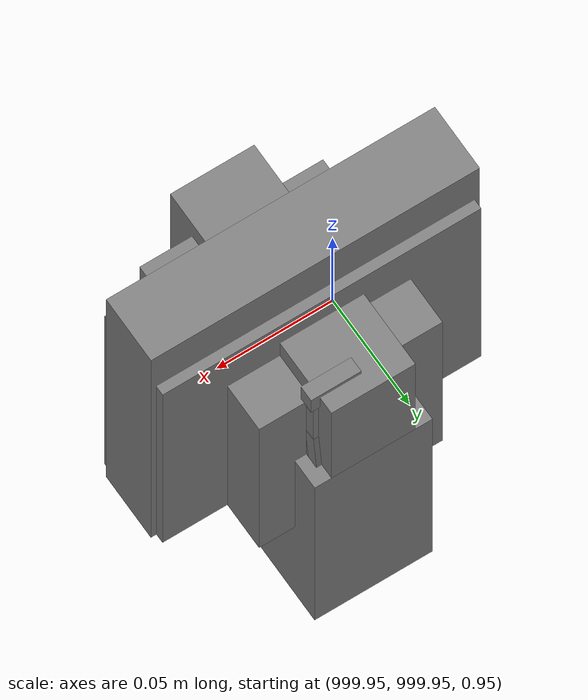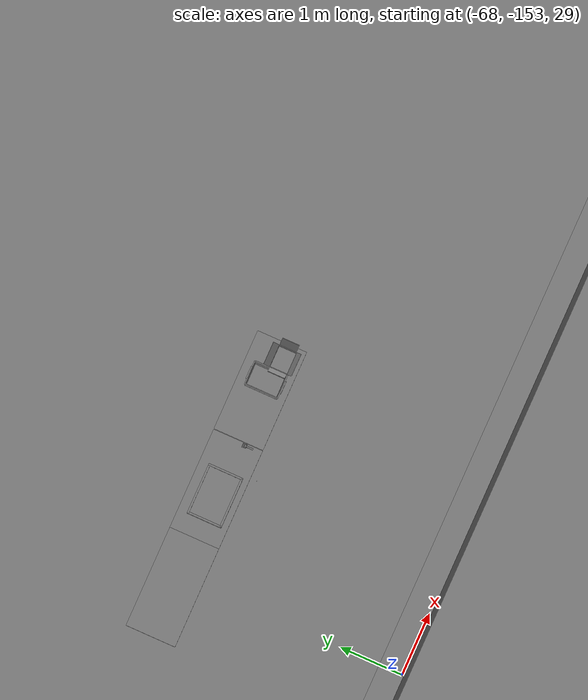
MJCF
<mujoco>
    <option gravity="0.000000000 0.000000000 -9.810000420" timestep="0.0049999999" integrator="implicitfast" density="1.225" viscosity="1.8000001e-05" noslip_iterations="10" iterations="100" sdf_iterations="50">
        <flag multiccd="disable"/>
    </option>
    <size memory="1000M"/>
    <compiler coordinate="local"/>
    <worldbody>
        <light cutoff="30" pos="0 1 1" dir="0 -1 -2"/>
        <light cutoff="30" pos="0 -1 1" dir="0 1 -2"/>
        <body pos="-64.866622925 -149.383972168 30.183746338" euler="89.999984741 89.999946594 0.000000000" name="openloong_gripper_2f85_fix_base_usda_bluebox_01">
            <geom contype="1" conaffinity="1" density="1000" type="box" material="" rgba="0.500000000 0.500000000 0.500000000 1.000000000" solimp="0.899999976 0.949999988 0.001000000" friction="1.000000000 0.005000000 0.000100000" solref="0.020000000 1.000000000" margin="0" condim="3" group="0" pos="0.276580811 0.187225342 0.000068665" quat="0.707106948 0.000077471 0.707106352 0.000077486" size="0.100000001 0.057999998 0.010000000" name="openloong_gripper_2f85_fix_base_usda_geom_12005A02_28F4_4893_8CCE_94266C1B622C"/>
            <geom contype="1" conaffinity="1" density="1000" type="box" material="" rgba="0.500000000 0.500000000 0.500000000 1.000000000" solimp="0.899999976 0.949999988 0.001000000" friction="1.000000000 0.005000000 0.000100000" solref="0.020000000 1.000000000" margin="0" condim="3" group="0" pos="0.000000000 0.002883911 0.000000000" quat="0.999999881 0.000000000 0.000000000 0.000000000" size="0.254000008 0.003000000 0.172000006" name="openloong_gripper_2f85_fix_base_usda_geom_D9A80975_65AC_4CA9_BFFC_3176AEE6AD27"/>
            <geom contype="1" conaffinity="1" density="1000" type="box" material="" rgba="0.500000000 0.500000000 0.500000000 1.000000000" solimp="0.899999976 0.949999988 0.001000000" friction="1.000000000 0.005000000 0.000100000" solref="0.020000000 1.000000000" margin="0" condim="3" group="0" pos="0.000000000 0.124874115 0.173484802" quat="0.999796331 0.020176515 -0.000000015 0.000000030" size="0.259999990 0.119999997 0.007000000" name="openloong_gripper_2f85_fix_base_usda_geom_70E4E6ED_8235_4094_8B3E_F6D1E3D2D58B"/>
            <geom contype="1" conaffinity="1" density="1000" type="box" material="" rgba="0.500000000 0.500000000 0.500000000 1.000000000" solimp="0.899999976 0.949999988 0.001000000" friction="1.000000000 0.005000000 0.000100000" solref="0.020000000 1.000000000" margin="0" condim="3" group="0" pos="0.000000000 0.124874115 -0.173469543" quat="0.999796331 -0.020176545 -0.000000015 0.000000000" size="0.259999990 0.119999997 0.007000000" name="openloong_gripper_2f85_fix_base_usda_geom_2F63DAA2_BA8C_42E9_9D67_C5D5857C697B"/>
            <geom contype="1" conaffinity="1" density="1000" type="box" material="" rgba="0.500000000 0.500000000 0.500000000 1.000000000" solimp="0.899999976 0.949999988 0.001000000" friction="1.000000000 0.005000000 0.000100000" solref="0.020000000 1.000000000" margin="0" condim="3" group="0" pos="0.000000000 0.214008331 0.188980103" quat="0.999912977 0.013176724 0.000000015 0.000000000" size="0.259999990 0.029999999 0.012500000" name="openloong_gripper_2f85_fix_base_usda_geom_B4E515A8_76A3_49D6_B678_0B6E1985C620"/>
            <geom contype="1" conaffinity="1" density="1000" type="box" material="" rgba="0.500000000 0.500000000 0.500000000 1.000000000" solimp="0.899999976 0.949999988 0.001000000" friction="1.000000000 0.005000000 0.000100000" solref="0.020000000 1.000000000" margin="0" condim="3" group="0" pos="-0.258361816 0.125289917 0.001876831" quat="0.702796936 -0.020792112 0.710783124 0.020769298" size="0.189999998 0.119999997 0.009000000" name="openloong_gripper_2f85_fix_base_usda_geom_70FAE9E9_E9F3_46C4_BD6B_83F471481448"/>
            <geom contype="1" conaffinity="1" density="1000" type="box" material="" rgba="0.500000000 0.500000000 0.500000000 1.000000000" solimp="0.899999976 0.949999988 0.001000000" friction="1.000000000 0.005000000 0.000100000" solref="0.020000000 1.000000000" margin="0" condim="3" group="0" pos="0.000000000 0.214008331 -0.188980103" quat="0.999912977 -0.013176769 0.000000030 0.000000015" size="0.259999990 0.029999999 0.012500000" name="openloong_gripper_2f85_fix_base_usda_geom_2F398582_28EE_4183_8AA5_454F83FD19DF"/>
            <geom contype="1" conaffinity="1" density="1000" type="box" material="" rgba="0.500000000 0.500000000 0.500000000 1.000000000" solimp="0.899999976 0.949999988 0.001000000" friction="1.000000000 0.005000000 0.000100000" solref="0.020000000 1.000000000" margin="0" condim="3" group="0" pos="-0.276611328 0.187225342 0.000068665" quat="0.707106650 0.000077441 0.707106709 0.000077456" size="0.100000001 0.057999998 0.010000000" name="openloong_gripper_2f85_fix_base_usda_geom_F740BC51_475B_4C5B_B9B4_CFDDBFDC0DF2"/>
            <geom contype="1" conaffinity="1" density="1000" type="box" material="" rgba="0.500000000 0.500000000 0.500000000 1.000000000" solimp="0.899999976 0.949999988 0.001000000" friction="1.000000000 0.005000000 0.000100000" solref="0.020000000 1.000000000" margin="0" condim="3" group="0" pos="0.258331299 0.125289917 0.001876831" quat="0.702851415 0.018856421 0.710823774 -0.019329369" size="0.189999998 0.119999997 0.009000000" name="openloong_gripper_2f85_fix_base_usda_geom_529520F3_F27E_4376_8DB9_CC35ADD2A63C"/>
            <freejoint name="openloong_gripper_2f85_fix_base_usda_bluebox_01_joint"/>
            <site size="0.005000000 0.005000000 0.005000000" rgba="0.500000000 0.500000000 0.500000000 1.000000000" pos="0.000000000 0.000000000 0.000000000" quat="0.999961913 0.008726534 0.000000000 0.000000000" group="0" type="sphere" name="openloong_gripper_2f85_fix_base_usda_bluebox_01site"/>
        </body>
        <body pos="-64.496299744 -149.491867065 30.235729218" euler="0.000000000 0.000000000 89.999946594" name="openloong_gripper_2f85_fix_base_usda_cardboardbox_01">
            <geom contype="1" conaffinity="1" density="1000" type="box" material="" rgba="0.500000000 0.500000000 0.500000000 1.000000000" solimp="0.899999976 0.949999988 0.001000000" friction="1.000000000 0.005000000 0.000100000" solref="0.020000000 1.000000000" margin="0" condim="3" group="0" pos="-0.003166199 -0.004086494 0.005052090" quat="1.000000000 0.000000000 0.000000000 0.000000000" size="0.142499998 0.177500010 0.005000000" name="openloong_gripper_2f85_fix_base_usda_geom_2FC1D355_62E5_4205_BDB8_EBBFB24AF959"/>
            <geom contype="1" conaffinity="1" density="1000" type="box" material="" rgba="0.500000000 0.500000000 0.500000000 1.000000000" solimp="0.899999976 0.949999988 0.001000000" friction="1.000000000 0.005000000 0.000100000" solref="0.020000000 1.000000000" margin="0" condim="3" group="0" pos="-0.003166199 0.170316696 0.150570869" quat="1.000000000 0.000000000 0.000000000 0.000000000" size="0.142499998 0.005000000 0.149999991" name="openloong_gripper_2f85_fix_base_usda_geom_55A67FEF_497F_4F0D_8E1E_1D8B7497DD50"/>
            <geom contype="1" conaffinity="1" density="1000" type="box" material="" rgba="0.500000000 0.500000000 0.500000000 1.000000000" solimp="0.899999976 0.949999988 0.001000000" friction="1.000000000 0.005000000 0.000100000" solref="0.020000000 1.000000000" margin="0" condim="3" group="0" pos="-0.147399902 -0.005307198 0.150570869" quat="1.000000000 0.000000000 0.000000000 0.000000000" size="0.005000000 0.177500010 0.149999991" name="openloong_gripper_2f85_fix_base_usda_geom_B6B77283_E21B_492C_A419_C597665AAB1B"/>
            <geom contype="1" conaffinity="1" density="1000" type="box" material="" rgba="0.500000000 0.500000000 0.500000000 1.000000000" solimp="0.899999976 0.949999988 0.001000000" friction="1.000000000 0.005000000 0.000100000" solref="0.020000000 1.000000000" margin="0" condim="3" group="0" pos="0.140275955 -0.005307198 0.150570869" quat="1.000000000 0.000000000 0.000000000 0.000000000" size="0.005000000 0.177500010 0.149999991" name="openloong_gripper_2f85_fix_base_usda_geom_D8E07D1C_5A70_410B_8A55_12ECFDE340C6"/>
            <geom contype="1" conaffinity="1" density="1000" type="box" material="" rgba="0.500000000 0.500000000 0.500000000 1.000000000" solimp="0.899999976 0.949999988 0.001000000" friction="1.000000000 0.005000000 0.000100000" solref="0.020000000 1.000000000" margin="0" condim="3" group="0" pos="-0.003166199 -0.181550980 0.150570869" quat="1.000000000 0.000000000 0.000000000 0.000000000" size="0.142499998 0.005000000 0.149999991" name="openloong_gripper_2f85_fix_base_usda_geom_F83707A6_217C_4663_A0E5_FDFC8547B3CC"/>
            <freejoint name="openloong_gripper_2f85_fix_base_usda_cardboardbox_01_joint"/>
            <site size="0.005000000 0.005000000 0.005000000" rgba="0.500000000 0.500000000 0.500000000 1.000000000" pos="0.000000000 0.000000000 0.000000000" quat="0.999961913 0.008726535 0.000000000 0.000000000" group="0" type="sphere" name="openloong_gripper_2f85_fix_base_usda_site_6F9EB455_3094_4873_8995_42A1F1C89369"/>
            <body pos="0.139160156 -0.004048347 0.301930904" euler="-179.999954224 49.383502960 179.999954224" name="openloong_gripper_2f85_fix_base_usda_A1_006">
                <geom contype="1" conaffinity="1" density="1000" type="box" material="" rgba="0.500000000 0.500000000 0.500000000 1.000000000" solimp="0.899999976 0.949999988 0.001000000" friction="1.000000000 0.005000000 0.000100000" solref="0.020000000 1.000000000" margin="0" condim="3" group="0" pos="-0.071587563 0.000009537 0.001745224" quat="0.999999881 0.000000000 0.000000000 0.000000000" size="0.071249999 0.179999992 0.002500000" name="openloong_gripper_2f85_fix_base_usda_geom_77BC2947_298A_4305_BC1F_E3D66714B10F"/>
                <joint armature="0" stiffness="0.07" damping="0.0099999998" axis="0.000000 1.000000 0.000000" type="hinge" name="openloong_gripper_2f85_fix_base_usda_A1_006"/>
            </body>
            <body pos="-0.145902634 -0.004086494 0.301938057" euler="-180.000000000 -60.000011444 -180.000000000" name="openloong_gripper_2f85_fix_base_usda_A2_006">
                <geom contype="1" conaffinity="1" density="1000" type="box" material="" rgba="0.500000000 0.500000000 0.500000000 1.000000000" solimp="0.899999976 0.949999988 0.001000000" friction="1.000000000 0.005000000 0.000100000" solref="0.020000000 1.000000000" margin="0" condim="3" group="0" pos="0.071268082 0.000009537 0.002717972" quat="0.000002921 0.000000000 -0.000000030 0.999999881" size="0.071249999 0.179999992 0.002500000" name="openloong_gripper_2f85_fix_base_usda_geom_3498BCDA_D59F_4CFE_AB80_A88DAFAE5CB8"/>
                <joint armature="0" stiffness="0.07" damping="0.0099999998" axis="0.000000 1.000000 0.000000" type="hinge" name="openloong_gripper_2f85_fix_base_usda_A2_006"/>
            </body>
            <body pos="-0.003385544 0.175991058 0.301930904" euler="-125.858116150 -0.000004561 0.000002331" name="openloong_gripper_2f85_fix_base_usda_B2_006">
                <geom contype="1" conaffinity="1" density="1000" type="box" material="" rgba="0.500000000 0.500000000 0.500000000 1.000000000" solimp="0.899999976 0.949999988 0.001000000" friction="1.000000000 0.005000000 0.000100000" solref="0.020000000 1.000000000" margin="0" condim="3" group="0" pos="0.000009537 -0.070939064 -0.002470016" quat="0.999614120 0.027776197 -0.000000015 0.000000030" size="0.137500003 0.064999998 0.005000000" name="openloong_gripper_2f85_fix_base_usda_geom_478B3A8E_FF5F_4C60_8A63_E99C64B36297"/>
                <joint armature="0" stiffness="0.07" damping="0.0099999998" axis="1.000000 0.000000 0.000000" type="hinge" name="openloong_gripper_2f85_fix_base_usda_B2_006"/>
            </body>
            <body pos="-0.003385544 -0.184140205 0.301938057" euler="147.805557251 0.000000000 0.000000000" name="openloong_gripper_2f85_fix_base_usda_B1_006">
                <geom contype="1" conaffinity="1" density="1000" type="box" material="" rgba="0.500000000 0.500000000 0.500000000 1.000000000" solimp="0.899999976 0.949999988 0.001000000" friction="1.000000000 0.005000000 0.000100000" solref="0.020000000 1.000000000" margin="0" condim="3" group="0" pos="-0.000028610 0.070202351 -0.002703667" quat="0.999614179 -0.027776167 0.000000000 0.000000000" size="0.137500003 0.064999998 0.005000000" name="openloong_gripper_2f85_fix_base_usda_geom_23CBFE2F_B041_413B_938B_507F17AA732A"/>
                <joint armature="0" stiffness="0.07" damping="0.0099999998" axis="1.000000 0.000000 0.000000" type="hinge" name="openloong_gripper_2f85_fix_base_usda_B1_006"/>
            </body>
        </body>
        <body pos="-65.882858276 -149.481979370 30.229999542" euler="-64.487716675 0.000000000 0.000000000" name="openloong_gripper_2f85_fix_base_usda_Barcode">
            <geom contype="1" conaffinity="1" density="1000" type="box" material="" rgba="0.500000000 0.500000000 0.500000000 1.000000000" solimp="0.899999976 0.949999988 0.001000000" friction="1.000000000 0.005000000 0.000100000" solref="0.020000000 1.000000000" margin="0" condim="3" group="0" pos="0.000000000 0.013038635 0.001419067" quat="0.000000000 0.000000000 0.000000000 1.000000119" size="0.034000002 0.010000000 0.017999999" name="openloong_gripper_2f85_fix_base_usda_geom_D70E68DB_88F5_4C7C_872C_CE34F14190AF"/>
            <geom contype="1" conaffinity="1" density="1000" type="box" material="" rgba="0.500000000 0.500000000 0.500000000 1.000000000" solimp="0.899999976 0.949999988 0.001000000" friction="1.000000000 0.005000000 0.000100000" solref="0.020000000 1.000000000" margin="0" condim="3" group="0" pos="0.000000000 -0.035301208 -0.007095337" quat="0.000000000 0.000000000 -0.043619365 0.999048233" size="0.028999999 0.010000000 0.020000000" name="openloong_gripper_2f85_fix_base_usda_geom_1EC90D2D_F947_449A_9608_010C4B2FDF08"/>
            <geom contype="1" conaffinity="1" density="1000" type="box" material="" rgba="0.500000000 0.500000000 0.500000000 1.000000000" solimp="0.899999976 0.949999988 0.001000000" friction="1.000000000 0.005000000 0.000100000" solref="0.020000000 1.000000000" margin="0" condim="3" group="0" pos="0.000000000 -0.043411255 -0.011749268" quat="0.922262907 0.386563420 0.000000000 0.000000000" size="0.026000001 0.010000000 0.020000000" name="openloong_gripper_2f85_fix_base_usda_geom_8A445398_4A55_43DF_91D1_AA2DCBDB3CC8"/>
            <geom contype="1" conaffinity="1" density="1000" type="box" material="" rgba="0.500000000 0.500000000 0.500000000 1.000000000" solimp="0.899999976 0.949999988 0.001000000" friction="1.000000000 0.005000000 0.000100000" solref="0.020000000 1.000000000" margin="0" condim="3" group="0" pos="0.000000000 -0.016967773 -0.031860352" quat="0.000000000 0.000000000 0.000000000 1.000000119" size="0.008000000 0.010000000 0.013000000" name="openloong_gripper_2f85_fix_base_usda_geom_46E061A1_79D2_4307_A948_7774DD82EC6B"/>
            <geom contype="1" conaffinity="1" density="1000" type="box" material="" rgba="0.500000000 0.500000000 0.500000000 1.000000000" solimp="0.899999976 0.949999988 0.001000000" friction="1.000000000 0.005000000 0.000100000" solref="0.020000000 1.000000000" margin="0" condim="3" group="0" pos="0.000000000 -0.001869202 0.000312805" quat="0.953716993 0.300705761 0.000000000 0.000000000" size="0.032000002 0.010000000 0.018999999" name="openloong_gripper_2f85_fix_base_usda_geom_56D4BCF1_059E_444C_992A_96384EB94DEF"/>
            <geom contype="1" conaffinity="1" density="1000" type="box" material="" rgba="0.500000000 0.500000000 0.500000000 1.000000000" solimp="0.899999976 0.949999988 0.001000000" friction="1.000000000 0.005000000 0.000100000" solref="0.020000000 1.000000000" margin="0" condim="3" group="0" pos="0.000000000 -0.019531250 -0.003173828" quat="0.953716993 0.300705761 0.000000000 0.000000000" size="0.030999999 0.010000000 0.020000000" name="openloong_gripper_2f85_fix_base_usda_geom_45ABFA22_6ABD_47D9_B3DA_82F8710D4977"/>
            <geom contype="1" conaffinity="1" density="1000" type="box" material="" rgba="0.500000000 0.500000000 0.500000000 1.000000000" solimp="0.899999976 0.949999988 0.001000000" friction="1.000000000 0.005000000 0.000100000" solref="0.020000000 1.000000000" margin="0" condim="3" group="0" pos="0.000000000 -0.035301208 -0.007095337" quat="0.953716993 0.300705761 0.000000000 0.000000000" size="0.028999999 0.010000000 0.020000000" name="openloong_gripper_2f85_fix_base_usda_geom_6CD0316E_FB1F_4946_925C_F0F2199DFA05"/>
            <geom contype="1" conaffinity="1" density="1000" type="box" material="" rgba="0.500000000 0.500000000 0.500000000 1.000000000" solimp="0.899999976 0.949999988 0.001000000" friction="1.000000000 0.005000000 0.000100000" solref="0.020000000 1.000000000" margin="0" condim="3" group="0" pos="0.000000000 -0.042617798 -0.071121216" quat="0.000000000 0.000000000 0.000000000 1.000000119" size="0.013000000 0.021000000 0.059999999" name="openloong_gripper_2f85_fix_base_usda_geom_2CEEE05E_25C6_45F2_9D8A_6BAB46C40305"/>
            <freejoint name="openloong_gripper_2f85_fix_base_usda_Barcode_joint"/>
            <site size="0.005000000 0.005000000 0.005000000" rgba="0.500000000 0.500000000 0.500000000 1.000000000" pos="0.000000000 0.000000000 0.000000000" quat="1.000000000 0.000000000 0.000000000 0.000000000" group="0" type="sphere" name="openloong_gripper_2f85_fix_base_usda_Barcode_site"/>
        </body>
        <body pos="-66.745018005 -149.392349243 30.184000015" euler="0.000000000 0.000000000 89.999946594" name="[22333313788528]_Basket_01">
            <geom contype="1" conaffinity="1" density="1000" type="box" material="" rgba="0.500000000 0.500000000 0.500000000 1.000000000" solimp="0.899999976 0.949999988 0.001000000" friction="1.000000000 0.005000000 0.000100000" solref="0.020000000 1.000000000" margin="0" condim="3" group="0" pos="-0.052425385 0.389207840 0.089787483" quat="0.707107008 0.000000000 0.000000000 0.707106411" size="0.014249999 0.014249999 0.059999999" name="[22333313788528]_geom_25A97BE0_2932_4461_B472_F5174C98792C"/>
            <geom contype="1" conaffinity="1" density="1000" type="box" material="" rgba="0.500000000 0.500000000 0.500000000 1.000000000" solimp="0.899999976 0.949999988 0.001000000" friction="1.000000000 0.005000000 0.000100000" solref="0.020000000 1.000000000" margin="0" condim="3" group="0" pos="0.264015198 -0.133043289 0.089787483" quat="0.707107008 0.000000000 0.000000000 0.707106411" size="0.014249999 0.014249999 0.059999999" name="[22333313788528]_geom_09C77E4E_6109_46CB_ADC1_CCB189954595"/>
            <geom contype="1" conaffinity="1" density="1000" type="box" material="" rgba="0.500000000 0.500000000 0.500000000 1.000000000" solimp="0.899999976 0.949999988 0.001000000" friction="1.000000000 0.005000000 0.000100000" solref="0.020000000 1.000000000" margin="0" condim="3" group="0" pos="-0.264015198 -0.265548706 0.089793205" quat="0.707107008 0.000000000 0.000000000 0.707106411" size="0.014249999 0.014249999 0.059999999" name="[22333313788528]_geom_B42DC32D_1A57_4CF9_B3CE_D208E4947D42"/>
            <geom contype="1" conaffinity="1" density="1000" type="box" material="" rgba="0.500000000 0.500000000 0.500000000 1.000000000" solimp="0.899999976 0.949999988 0.001000000" friction="1.000000000 0.005000000 0.000100000" solref="0.020000000 1.000000000" margin="0" condim="3" group="0" pos="-0.160263062 -0.389322281 0.089793205" quat="0.707107008 0.000000000 0.000000000 0.707106411" size="0.014249999 0.014249999 0.059999999" name="[22333313788528]_geom_45952037_2B83_4F17_B490_16E53F76BFB3"/>
            <geom contype="1" conaffinity="1" density="1000" type="box" material="" rgba="0.500000000 0.500000000 0.500000000 1.000000000" solimp="0.899999976 0.949999988 0.001000000" friction="1.000000000 0.005000000 0.000100000" solref="0.020000000 1.000000000" margin="0" condim="3" group="0" pos="0.162265778 -0.389322281 0.089787483" quat="0.707107008 0.000000000 0.000000000 0.707106411" size="0.014249999 0.014249999 0.059999999" name="[22333313788528]_geom_D909F56A_1EA3_400F_9CBF_F5809329496A"/>
            <geom contype="1" conaffinity="1" density="1000" type="box" material="" rgba="0.500000000 0.500000000 0.500000000 1.000000000" solimp="0.899999976 0.949999988 0.001000000" friction="1.000000000 0.005000000 0.000100000" solref="0.020000000 1.000000000" margin="0" condim="3" group="0" pos="0.264015198 0.389207840 0.089787483" quat="0.707107008 0.000000000 0.000000000 0.707106411" size="0.014249999 0.014249999 0.059999999" name="[22333313788528]_geom_AF3410AB_6234_459F_9353_6F6B02DD21FC"/>
            <geom contype="1" conaffinity="1" density="1000" type="box" material="" rgba="0.500000000 0.500000000 0.500000000 1.000000000" solimp="0.899999976 0.949999988 0.001000000" friction="1.000000000 0.005000000 0.000100000" solref="0.020000000 1.000000000" margin="0" condim="3" group="0" pos="-0.264015198 -0.133043289 0.089793205" quat="0.707107008 0.000000000 0.000000000 0.707106411" size="0.014249999 0.014249999 0.059999999" name="[22333313788528]_geom_A6C0B9A9_EAF2_40F1_8C7E_4A99DF1E694E"/>
            <geom contype="1" conaffinity="1" density="1000" type="box" material="" rgba="0.500000000 0.500000000 0.500000000 1.000000000" solimp="0.899999976 0.949999988 0.001000000" friction="1.000000000 0.005000000 0.000100000" solref="0.020000000 1.000000000" margin="0" condim="3" group="0" pos="-0.264026642 0.269256592 0.089793205" quat="0.707107008 0.000000000 0.000000000 0.707106411" size="0.014249999 0.014249999 0.059999999" name="[22333313788528]_geom_376BF873_E382_47C6_AFDA_A98B22542605"/>
            <geom contype="1" conaffinity="1" density="1000" type="box" material="" rgba="0.500000000 0.500000000 0.500000000 1.000000000" solimp="0.899999976 0.949999988 0.001000000" friction="1.000000000 0.005000000 0.000100000" solref="0.020000000 1.000000000" margin="0" condim="3" group="0" pos="0.054462433 0.389207840 0.089787483" quat="0.707107008 0.000000000 0.000000000 0.707106411" size="0.014249999 0.014249999 0.059999999" name="[22333313788528]_geom_4D45A0CB_73DD_418E_B35B_2E00CC8A74D4"/>
            <geom contype="1" conaffinity="1" density="1000" type="box" material="" rgba="0.500000000 0.500000000 0.500000000 1.000000000" solimp="0.899999976 0.949999988 0.001000000" friction="1.000000000 0.005000000 0.000100000" solref="0.020000000 1.000000000" margin="0" condim="3" group="0" pos="0.054462433 -0.389322281 0.089787483" quat="0.707107008 0.000000000 0.000000000 0.707106411" size="0.014249999 0.014249999 0.059999999" name="[22333313788528]_geom_DC309568_44BB_4173_B229_C0E34C1578E2"/>
            <geom contype="1" conaffinity="1" density="1000" type="box" material="" rgba="0.500000000 0.500000000 0.500000000 1.000000000" solimp="0.899999976 0.949999988 0.001000000" friction="1.000000000 0.005000000 0.000100000" solref="0.020000000 1.000000000" margin="0" condim="3" group="0" pos="0.264015198 0.269256592 0.089793205" quat="0.707107008 0.000000000 0.000000000 0.707106411" size="0.014249999 0.014249999 0.059999999" name="[22333313788528]_geom_8E760B90_CB5C_474B_AD15_7F00B7B024AE"/>
            <geom contype="1" conaffinity="1" density="1000" type="box" material="" rgba="0.500000000 0.500000000 0.500000000 1.000000000" solimp="0.899999976 0.949999988 0.001000000" friction="1.000000000 0.005000000 0.000100000" solref="0.020000000 1.000000000" margin="0" condim="3" group="0" pos="0.264015198 -0.389322281 0.089787483" quat="0.707107008 0.000000000 0.000000000 0.707106411" size="0.014249999 0.014249999 0.059999999" name="[22333313788528]_geom_BAB2EE1A_ACD1_4A82_8D80_2D7874687EDE"/>
            <geom contype="1" conaffinity="1" density="1000" type="box" material="" rgba="0.500000000 0.500000000 0.500000000 1.000000000" solimp="0.899999976 0.949999988 0.001000000" friction="1.000000000 0.005000000 0.000100000" solref="0.020000000 1.000000000" margin="0" condim="3" group="0" pos="0.000000000 0.000000000 0.015998840" quat="0.707107008 0.000000000 0.000000000 0.707106411" size="0.403499991 0.279000014 0.015750000" name="[22333313788528]_geom_C6761029_E672_40D2_9543_25386B046E98"/>
            <geom contype="1" conaffinity="1" density="1000" type="box" material="" rgba="0.500000000 0.500000000 0.500000000 1.000000000" solimp="0.899999976 0.949999988 0.001000000" friction="1.000000000 0.005000000 0.000100000" solref="0.020000000 1.000000000" margin="0" condim="3" group="0" pos="0.000000000 -0.389476776 0.163619041" quat="0.707107008 0.000000000 0.000000000 0.707106411" size="0.015000000 0.277500004 0.015750000" name="[22333313788528]_geom_66309FF8_C3B7_4C26_A0DE_BD82991BC13C"/>
            <geom contype="1" conaffinity="1" density="1000" type="box" material="" rgba="0.500000000 0.500000000 0.500000000 1.000000000" solimp="0.899999976 0.949999988 0.001000000" friction="1.000000000 0.005000000 0.000100000" solref="0.020000000 1.000000000" margin="0" condim="3" group="0" pos="0.162265778 0.389207840 0.089787483" quat="0.707107008 0.000000000 0.000000000 0.707106411" size="0.014249999 0.014249999 0.059999999" name="[22333313788528]_geom_60B3054E_3EFB_4C89_9B6F_94AC62334750"/>
            <geom contype="1" conaffinity="1" density="1000" type="box" material="" rgba="0.500000000 0.500000000 0.500000000 1.000000000" solimp="0.899999976 0.949999988 0.001000000" friction="1.000000000 0.005000000 0.000100000" solref="0.020000000 1.000000000" margin="0" condim="3" group="0" pos="0.000000000 0.389471054 0.163619041" quat="0.707107008 0.000000000 0.000000000 0.707106411" size="0.015000000 0.277500004 0.015750000" name="[22333313788528]_geom_AB8468BA_A52F_443C_83C5_231A891E01F0"/>
            <geom contype="1" conaffinity="1" density="1000" type="box" material="" rgba="0.500000000 0.500000000 0.500000000 1.000000000" solimp="0.899999976 0.949999988 0.001000000" friction="1.000000000 0.005000000 0.000100000" solref="0.020000000 1.000000000" margin="0" condim="3" group="0" pos="-0.263511658 0.000000000 0.163619041" quat="0.707107008 0.000000000 0.000000000 0.707106411" size="0.403499991 0.015000000 0.015750000" name="[22333313788528]_geom_11D778CF_02BF_4CE7_81F0_65CD2501628D"/>
            <geom contype="1" conaffinity="1" density="1000" type="box" material="" rgba="0.500000000 0.500000000 0.500000000 1.000000000" solimp="0.899999976 0.949999988 0.001000000" friction="1.000000000 0.005000000 0.000100000" solref="0.020000000 1.000000000" margin="0" condim="3" group="0" pos="-0.264015198 0.141334534 0.089793205" quat="0.707107008 0.000000000 0.000000000 0.707106411" size="0.014249999 0.014249999 0.059999999" name="[22333313788528]_geom_5C505549_44C9_4AC4_907D_85C668BAB800"/>
            <geom contype="1" conaffinity="1" density="1000" type="box" material="" rgba="0.500000000 0.500000000 0.500000000 1.000000000" solimp="0.899999976 0.949999988 0.001000000" friction="1.000000000 0.005000000 0.000100000" solref="0.020000000 1.000000000" margin="0" condim="3" group="0" pos="0.264015198 -0.265548706 0.089787483" quat="0.707107008 0.000000000 0.000000000 0.707106411" size="0.014249999 0.014249999 0.059999999" name="[22333313788528]_geom_94785182_BEDF_4D0A_BF1D_25206DCB0F7E"/>
            <geom contype="1" conaffinity="1" density="1000" type="box" material="" rgba="0.500000000 0.500000000 0.500000000 1.000000000" solimp="0.899999976 0.949999988 0.001000000" friction="1.000000000 0.005000000 0.000100000" solref="0.020000000 1.000000000" margin="0" condim="3" group="0" pos="-0.160263062 0.389207840 0.089787483" quat="0.707107008 0.000000000 0.000000000 0.707106411" size="0.014249999 0.014249999 0.059999999" name="[22333313788528]_geom_BB466517_87E9_41A2_96A6_C44F11E74EA9"/>
            <geom contype="1" conaffinity="1" density="1000" type="box" material="" rgba="0.500000000 0.500000000 0.500000000 1.000000000" solimp="0.899999976 0.949999988 0.001000000" friction="1.000000000 0.005000000 0.000100000" solref="0.020000000 1.000000000" margin="0" condim="3" group="0" pos="-0.052425385 -0.389322281 0.089787483" quat="0.707107008 0.000000000 0.000000000 0.707106411" size="0.014249999 0.014249999 0.059999999" name="[22333313788528]_geom_AA3FAB8A_6844_4611_B723_AEBB36496B9C"/>
            <geom contype="1" conaffinity="1" density="1000" type="box" material="" rgba="0.500000000 0.500000000 0.500000000 1.000000000" solimp="0.899999976 0.949999988 0.001000000" friction="1.000000000 0.005000000 0.000100000" solref="0.020000000 1.000000000" margin="0" condim="3" group="0" pos="-0.264026642 -0.389322281 0.089793205" quat="0.707107008 0.000000000 0.000000000 0.707106411" size="0.014249999 0.014249999 0.059999999" name="[22333313788528]_geom_28A6A54E_6A13_49A2_83BD_63D12ED4430C"/>
            <geom contype="1" conaffinity="1" density="1000" type="box" material="" rgba="0.500000000 0.500000000 0.500000000 1.000000000" solimp="0.899999976 0.949999988 0.001000000" friction="1.000000000 0.005000000 0.000100000" solref="0.020000000 1.000000000" margin="0" condim="3" group="0" pos="0.264015198 0.141334534 0.089787483" quat="0.707107008 0.000000000 0.000000000 0.707106411" size="0.014249999 0.014249999 0.059999999" name="[22333313788528]_geom_A3069C22_CF25_44A3_8F21_31E2619FDD22"/>
            <geom contype="1" conaffinity="1" density="1000" type="box" material="" rgba="0.500000000 0.500000000 0.500000000 1.000000000" solimp="0.899999976 0.949999988 0.001000000" friction="1.000000000 0.005000000 0.000100000" solref="0.020000000 1.000000000" margin="0" condim="3" group="0" pos="-0.264015198 0.389207840 0.089793205" quat="0.707107008 0.000000000 0.000000000 0.707106411" size="0.014249999 0.014249999 0.059999999" name="[22333313788528]_geom_DDE5D802_7E12_4FD4_B93B_85FE19495A90"/>
            <geom contype="1" conaffinity="1" density="1000" type="box" material="" rgba="0.500000000 0.500000000 0.500000000 1.000000000" solimp="0.899999976 0.949999988 0.001000000" friction="1.000000000 0.005000000 0.000100000" solref="0.020000000 1.000000000" margin="0" condim="3" group="0" pos="0.264015198 0.004480362 0.089787483" quat="0.707107008 0.000000000 0.000000000 0.707106411" size="0.014249999 0.014249999 0.059999999" name="[22333313788528]_geom_ED60C4B1_CF0B_4EF5_A613_FA353DFF09B7"/>
            <geom contype="1" conaffinity="1" density="1000" type="box" material="" rgba="0.500000000 0.500000000 0.500000000 1.000000000" solimp="0.899999976 0.949999988 0.001000000" friction="1.000000000 0.005000000 0.000100000" solref="0.020000000 1.000000000" margin="0" condim="3" group="0" pos="0.263694763 -0.000011444 0.163619041" quat="0.707107008 0.000000000 0.000000000 0.707106411" size="0.403499991 0.015000000 0.015750000" name="[22333313788528]_geom_97E93449_F1B5_4C04_A006_B4F69DCC1F34"/>
            <geom contype="1" conaffinity="1" density="1000" type="box" material="" rgba="0.500000000 0.500000000 0.500000000 1.000000000" solimp="0.899999976 0.949999988 0.001000000" friction="1.000000000 0.005000000 0.000100000" solref="0.020000000 1.000000000" margin="0" condim="3" group="0" pos="-0.264015198 0.004480362 0.089793205" quat="0.707107008 0.000000000 0.000000000 0.707106411" size="0.014249999 0.014249999 0.059999999" name="[22333313788528]_geom_1465A576_38D0_4E1A_B6AC_D9B76A03D991"/>
            <freejoint name="[22333313788528]_joint_9671D2DD_CCD3_422B_B9FB_834042BA7472"/>
        </body>
        <body pos="0.000000000 0.000000000 0.000000000" euler="0.000000000 0.000000000 0.000000000" name="Static Objects_Static Objects">
            <geom contype="1" conaffinity="1" density="1000" type="box" material="" rgba="0.500000000 0.500000000 0.500000000 1.000000000" solimp="0.899999976 0.949999988 0.001000000" friction="1.000000000 0.005000000 0.000100000" solref="0.020000000 1.000000000" margin="0" condim="3" group="0" pos="-67.544113159 -149.365814209 29.727830887" quat="0.500000417 0.499999970 0.499999553 0.499999970" size="0.381000012 0.319999993 0.041000001" name="Static Objects_geom_280A21F7_437F_4C7F_B5F2_AD43719DFFB0"/>
            <geom contype="1" conaffinity="1" density="1000" type="box" material="" rgba="0.500000000 0.500000000 0.500000000 1.000000000" solimp="0.899999976 0.949999988 0.001000000" friction="1.000000000 0.005000000 0.000100000" solref="0.020000000 1.000000000" margin="0" condim="3" group="0" pos="-68.239501953 -149.365814209 30.086868286" quat="0.500000417 0.499999970 0.499999553 0.499999970" size="0.370999992 0.039500002 0.745000005" name="Static Objects_geom_2FBF0142_8092_481E_A1CE_CF62E21D2BD2"/>
            <geom contype="1" conaffinity="1" density="1000" type="box" material="" rgba="0.500000000 0.500000000 0.500000000 1.000000000" solimp="0.899999976 0.949999988 0.001000000" friction="1.000000000 0.005000000 0.000100000" solref="0.020000000 1.000000000" margin="0" condim="3" group="0" pos="-68.239501953 -149.365814209 30.147235870" quat="0.500000417 0.499999970 0.499999553 0.499999970" size="0.400000006 0.022000000 0.800000012" name="Static Objects_geom_57CF07AC_122D_4687_B04E_8659C98FA3CF"/>
            <geom contype="1" conaffinity="1" density="1000" type="box" material="" rgba="0.500000000 0.500000000 0.500000000 1.000000000" solimp="0.899999976 0.949999988 0.001000000" friction="1.000000000 0.005000000 0.000100000" solref="0.020000000 1.000000000" margin="0" condim="3" group="0" pos="-68.934890747 -149.365814209 29.727830887" quat="0.500000417 0.499999970 0.499999553 0.499999970" size="0.381000012 0.319999993 0.041000001" name="Static Objects_geom_0C06ACAC_8B34_49AD_B886_C714A6E3E6DF"/>
            <geom contype="1" conaffinity="1" density="1000" type="box" material="" rgba="0.500000000 0.500000000 0.500000000 1.000000000" solimp="0.899999976 0.949999988 0.001000000" friction="1.000000000 0.005000000 0.000100000" solref="0.020000000 1.000000000" margin="0" condim="3" group="0" pos="-68.239501953 -149.365814209 29.561563492" quat="0.500000417 0.499999970 0.499999553 0.499999970" size="0.020000000 0.022000000 0.660000026" name="Static Objects_geom_55925341_5769_440D_8784_4876357599B3"/>
            <geom contype="1" conaffinity="1" density="1000" type="box" material="" rgba="0.500000000 0.500000000 0.500000000 1.000000000" solimp="0.899999976 0.949999988 0.001000000" friction="1.000000000 0.005000000 0.000100000" solref="0.020000000 1.000000000" margin="0" condim="3" group="0" pos="-65.945671082 -149.365814209 29.727830887" quat="0.500000417 0.499999970 0.499999553 0.499999970" size="0.381000012 0.319999993 0.041000001" name="Static Objects_geom_1FA589A4_0D45_4F2B_AEEF_9DCE373ADB07"/>
            <geom contype="1" conaffinity="1" density="1000" type="box" material="" rgba="0.500000000 0.500000000 0.500000000 1.000000000" solimp="0.899999976 0.949999988 0.001000000" friction="1.000000000 0.005000000 0.000100000" solref="0.020000000 1.000000000" margin="0" condim="3" group="0" pos="-66.641059875 -149.365814209 30.086868286" quat="0.500000417 0.499999970 0.499999553 0.499999970" size="0.370999992 0.039500002 0.745000005" name="Static Objects_geom_7F726424_E503_4725_8350_7FEC41505CDF"/>
            <geom contype="1" conaffinity="1" density="1000" type="box" material="" rgba="0.500000000 0.500000000 0.500000000 1.000000000" solimp="0.899999976 0.949999988 0.001000000" friction="1.000000000 0.005000000 0.000100000" solref="0.020000000 1.000000000" margin="0" condim="3" group="0" pos="-66.641059875 -149.365814209 30.147235870" quat="0.500000417 0.499999970 0.499999553 0.499999970" size="0.400000006 0.022000000 0.800000012" name="Static Objects_geom_FAB58273_B242_4367_8A5E_02C78CFD1248"/>
            <geom contype="1" conaffinity="1" density="1000" type="box" material="" rgba="0.500000000 0.500000000 0.500000000 1.000000000" solimp="0.899999976 0.949999988 0.001000000" friction="1.000000000 0.005000000 0.000100000" solref="0.020000000 1.000000000" margin="0" condim="3" group="0" pos="-67.336448669 -149.365814209 29.727830887" quat="0.500000417 0.499999970 0.499999553 0.499999970" size="0.381000012 0.319999993 0.041000001" name="Static Objects_geom_564F5057_E752_4481_8581_8BB9645655B2"/>
            <geom contype="1" conaffinity="1" density="1000" type="box" material="" rgba="0.500000000 0.500000000 0.500000000 1.000000000" solimp="0.899999976 0.949999988 0.001000000" friction="1.000000000 0.005000000 0.000100000" solref="0.020000000 1.000000000" margin="0" condim="3" group="0" pos="-66.641059875 -149.365814209 29.561563492" quat="0.500000417 0.499999970 0.499999553 0.499999970" size="0.020000000 0.022000000 0.660000026" name="Static Objects_geom_3EFB1F8D_1B35_48BB_B9A9_9B05E2430E2E"/>
            <geom contype="1" conaffinity="1" density="1000" type="box" material="" rgba="0.500000000 0.500000000 0.500000000 1.000000000" solimp="0.899999976 0.949999988 0.001000000" friction="1.000000000 0.005000000 0.000100000" solref="0.020000000 1.000000000" margin="0" condim="3" group="0" pos="-64.338577271 -149.365814209 29.727830887" quat="0.500000417 0.499999970 0.499999553 0.499999970" size="0.381000012 0.319999993 0.041000001" name="Static Objects_geom_510DBEA5_D9E0_4833_9131_28E40AA92FDF"/>
            <geom contype="1" conaffinity="1" density="1000" type="box" material="" rgba="0.500000000 0.500000000 0.500000000 1.000000000" solimp="0.899999976 0.949999988 0.001000000" friction="1.000000000 0.005000000 0.000100000" solref="0.020000000 1.000000000" margin="0" condim="3" group="0" pos="-65.033966064 -149.365814209 30.086868286" quat="0.500000417 0.499999970 0.499999553 0.499999970" size="0.370999992 0.039500002 0.745000005" name="Static Objects_geom_36D7B0AB_AFB0_4A35_8E83_CA9AF8EAC4DA"/>
            <geom contype="1" conaffinity="1" density="1000" type="box" material="" rgba="0.500000000 0.500000000 0.500000000 1.000000000" solimp="0.899999976 0.949999988 0.001000000" friction="1.000000000 0.005000000 0.000100000" solref="0.020000000 1.000000000" margin="0" condim="3" group="0" pos="-65.033966064 -149.365814209 30.147235870" quat="0.500000417 0.499999970 0.499999553 0.499999970" size="0.400000006 0.022000000 0.800000012" name="Static Objects_geom_2005FD5F_F76F_4647_8978_D048FFB6828F"/>
            <geom contype="1" conaffinity="1" density="1000" type="box" material="" rgba="0.500000000 0.500000000 0.500000000 1.000000000" solimp="0.899999976 0.949999988 0.001000000" friction="1.000000000 0.005000000 0.000100000" solref="0.020000000 1.000000000" margin="0" condim="3" group="0" pos="-65.729354858 -149.365814209 29.727830887" quat="0.500000417 0.499999970 0.499999553 0.499999970" size="0.381000012 0.319999993 0.041000001" name="Static Objects_geom_8FF82072_999F_4CAD_A06E_A8A1A15734BC"/>
            <geom contype="1" conaffinity="1" density="1000" type="box" material="" rgba="0.500000000 0.500000000 0.500000000 1.000000000" solimp="0.899999976 0.949999988 0.001000000" friction="1.000000000 0.005000000 0.000100000" solref="0.020000000 1.000000000" margin="0" condim="3" group="0" pos="-65.033966064 -149.365814209 29.561563492" quat="0.500000417 0.499999970 0.499999553 0.499999970" size="0.020000000 0.022000000 0.660000026" name="Static Objects_geom_DE7C64A3_5D1D_4FB5_8E89_4D69C5C1931F"/>
            <geom contype="1" conaffinity="1" density="1000" type="box" material="" rgba="0.500000000 0.500000000 0.500000000 1.000000000" solimp="0.899999976 0.949999988 0.001000000" friction="1.000000000 0.005000000 0.000100000" solref="0.020000000 1.000000000" margin="0" condim="3" group="0" pos="-61.754566193 -137.853729248 33.906845093" quat="0.707107067 0.000000000 0.000000000 0.707106471" size="0.759999990 0.759999990 4.500000000" name="Static Objects_geom_0085E763_B976_425C_9516_9687BF31BCB8"/>
            <geom contype="1" conaffinity="1" density="1000" type="box" material="" rgba="0.500000000 0.500000000 0.500000000 1.000000000" solimp="0.899999976 0.949999988 0.001000000" friction="1.000000000 0.005000000 0.000100000" solref="0.020000000 1.000000000" margin="0" condim="3" group="0" pos="-57.511135101 -144.927108765 31.707921982" quat="1.000000000 0.000000000 0.000000000 0.000000000" size="0.200000003 8.000000000 2.299999952" name="Static Objects_geom_A45ACCED_0D94_4249_BA4B_7F44425BF129"/>
            <geom contype="1" conaffinity="1" density="1000" type="box" material="" rgba="0.500000000 0.500000000 0.500000000 1.000000000" solimp="0.899999976 0.949999988 0.001000000" friction="1.000000000 0.005000000 0.000100000" solref="0.020000000 1.000000000" margin="0" condim="3" group="0" pos="-80.517646790 -157.574050903 31.688196182" quat="0.707107067 0.000000000 0.000000000 0.707106471" size="0.600000024 0.600000024 2.299999952" name="Static Objects_geom_91E34F8E_EBBB_46F6_A8E5_B4E1681BCE3D"/>
            <geom contype="1" conaffinity="1" density="1000" type="box" material="" rgba="0.500000000 0.500000000 0.500000000 1.000000000" solimp="0.899999976 0.949999988 0.001000000" friction="1.000000000 0.005000000 0.000100000" solref="0.020000000 1.000000000" margin="0" condim="3" group="0" pos="-80.711044312 -147.414932251 31.666158676" quat="1.000000000 0.000000000 0.000000000 0.000000000" size="0.200000003 10.000000000 2.299999952" name="Static Objects_geom_26A5C296_2F98_441A_9E7F_A3E7FACE46F3"/>
            <geom contype="1" conaffinity="1" density="1000" type="box" material="" rgba="0.500000000 0.500000000 0.500000000 1.000000000" solimp="0.899999976 0.949999988 0.001000000" friction="1.000000000 0.005000000 0.000100000" solref="0.020000000 1.000000000" margin="0" condim="3" group="0" pos="-57.687217712 -137.434692383 31.688196182" quat="0.707107067 0.000000000 0.000000000 0.707106471" size="0.600000024 0.600000024 2.299999952" name="Static Objects_geom_3A74F42C_C4AF_4EB0_BEBE_C05D347290C7"/>
            <geom contype="1" conaffinity="1" density="1000" type="box" material="" rgba="0.500000000 0.500000000 0.500000000 1.000000000" solimp="0.899999976 0.949999988 0.001000000" friction="1.000000000 0.005000000 0.000100000" solref="0.020000000 1.000000000" margin="0" condim="3" group="0" pos="-69.537033081 -140.263229370 31.714921951" quat="0.707107067 0.000000000 0.000000000 0.707106471" size="0.759999990 4.500000000 2.299999952" name="Static Objects_geom_08B2D180_2959_4314_A66C_C87EFB11636B"/>
            <geom contype="1" conaffinity="1" density="1000" type="box" material="" rgba="0.500000000 0.500000000 0.500000000 1.000000000" solimp="0.899999976 0.949999988 0.001000000" friction="1.000000000 0.005000000 0.000100000" solref="0.020000000 1.000000000" margin="0" condim="3" group="0" pos="-80.073638916 -137.853713989 33.906845093" quat="0.707107067 0.000000000 0.000000000 0.707106471" size="0.759999990 0.759999990 4.500000000" name="Static Objects_geom_BC5AAADA_1111_460E_AAA5_8708842CAF3F"/>
            <geom contype="1" conaffinity="1" density="1000" type="box" material="" rgba="0.500000000 0.500000000 0.500000000 1.000000000" solimp="0.899999976 0.949999988 0.001000000" friction="1.000000000 0.005000000 0.000100000" solref="0.020000000 1.000000000" margin="0" condim="3" group="0" pos="-73.406707764 -155.734664917 31.707921982" quat="1.000000000 0.000000000 0.000000000 0.000000000" size="0.200000003 3.000000000 2.299999952" name="Static Objects_geom_A89C1DAE_9A6F_4984_88A2_9CBE995EF16F"/>
            <geom contype="1" conaffinity="1" density="1000" type="box" material="" rgba="0.500000000 0.500000000 0.500000000 1.000000000" solimp="0.899999976 0.949999988 0.001000000" friction="1.000000000 0.005000000 0.000100000" solref="0.020000000 1.000000000" margin="0" condim="3" group="0" pos="-68.497543335 -137.448257446 31.707921982" quat="0.707107067 0.000000000 0.000000000 0.707106471" size="0.200000003 14.000000000 2.299999952" name="Static Objects_geom_F2399DF1_421A_4810_A2F2_FF9CA8F57C32"/>
            <geom contype="1" conaffinity="1" density="1000" type="cylinder" material="" rgba="0.500000000 0.500000000 0.500000000 1.000000000" solimp="0.899999976 0.949999988 0.001000000" friction="1.000000000 0.005000000 0.000100000" solref="0.020000000 1.000000000" margin="0" condim="3" group="0" pos="-68.868522644 -142.134506226 31.711090088" quat="0.707107067 0.000000000 0.000000000 0.707106471" size="0.509999990 2.299999952 1.000000000" name="Static Objects_geom_A776AB95_4534_4C4B_9A6E_969CED9C26F5"/>
            <geom contype="1" conaffinity="1" density="1000" type="plane" material="" rgba="0.500000000 0.500000000 0.500000000 1.000000000" solimp="0.899999976 0.949999988 0.001000000" friction="1.000000000 0.005000000 0.000100000" solref="0.020000000 1.000000000" margin="0" condim="3" group="0" pos="-72.873703003 -147.131927490 29.409669876" quat="1.000000000 0.000000000 0.000000000 0.000000000" size="18.000000000 14.000000000 1.000000000" name="Static Objects_geom_642999CC_ECA3_4E8A_BCF0_04C8510B9C08"/>
            <geom contype="1" conaffinity="1" density="1000" type="box" material="" rgba="0.500000000 0.500000000 0.500000000 1.000000000" solimp="0.899999976 0.949999988 0.001000000" friction="1.000000000 0.005000000 0.000100000" solref="0.020000000 1.000000000" margin="0" condim="3" group="0" pos="-79.943580627 -157.782272339 31.707921982" quat="0.707107067 0.000000000 0.000000000 0.707106471" size="0.200000003 7.000000000 2.299999952" name="Static Objects_geom_FD3F14BE_B139_45DD_9B80_2A91913FB9C3"/>
            <geom contype="1" conaffinity="1" density="1000" type="box" material="" rgba="0.500000000 0.500000000 0.500000000 1.000000000" solimp="0.899999976 0.949999988 0.001000000" friction="1.000000000 0.005000000 0.000100000" solref="0.020000000 1.000000000" margin="0" condim="3" group="0" pos="-65.421028137 -152.903442383 31.707921982" quat="0.707107067 0.000000000 0.000000000 0.707106471" size="0.200000003 7.800000191 2.299999952" name="Static Objects_geom_15A6E442_F344_4666_946D_D880B1121E96"/>
            <geom contype="1" conaffinity="1" density="1000" type="box" material="" rgba="0.500000000 0.500000000 0.500000000 1.000000000" solimp="0.899999976 0.949999988 0.001000000" friction="1.000000000 0.005000000 0.000100000" solref="0.020000000 1.000000000" margin="0" condim="3" group="0" pos="-74.776908875 -149.964416504 31.688196182" quat="1.000000000 0.000000000 0.000000000 0.000000000" size="0.600000024 0.409999996 2.299999952" name="Static Objects_geom_B0DAF05B_9FE5_4739_8B69_503C86347F5C"/>
            <geom contype="1" conaffinity="1" density="1000" type="cylinder" material="" rgba="0.500000000 0.500000000 0.500000000 1.000000000" solimp="0.899999976 0.949999988 0.001000000" friction="1.000000000 0.005000000 0.000100000" solref="0.020000000 1.000000000" margin="0" condim="3" group="0" pos="-60.161884308 -142.134506226 31.711090088" quat="0.707107067 0.000000000 0.000000000 0.707106471" size="0.509999990 2.299999952 1.000000000" name="Static Objects_geom_3D21ED6D_2A68_44B6_BC93_199B65774AE3"/>
            <geom contype="1" conaffinity="1" density="1000" type="cylinder" material="" rgba="0.500000000 0.500000000 0.500000000 1.000000000" solimp="0.899999976 0.949999988 0.001000000" friction="1.000000000 0.005000000 0.000100000" solref="0.020000000 1.000000000" margin="0" condim="3" group="0" pos="-75.382453918 -149.963455200 31.711090088" quat="0.707107067 0.000000000 0.000000000 0.707106471" size="0.409999996 2.299999952 1.000000000" name="Static Objects_geom_E1093425_4092_4554_8F18_77749499D224"/>
            <geom contype="1" conaffinity="1" density="1000" type="cylinder" material="" rgba="0.500000000 0.500000000 0.500000000 1.000000000" solimp="0.899999976 0.949999988 0.001000000" friction="1.000000000 0.005000000 0.000100000" solref="0.020000000 1.000000000" margin="0" condim="3" group="0" pos="-74.154960632 -149.963455200 31.711090088" quat="0.707107067 0.000000000 0.000000000 0.707106471" size="0.409999996 2.299999952 1.000000000" name="Static Objects_geom_D27C960F_BFAC_4804_A492_688410238CAE"/>
            <geom contype="1" conaffinity="1" density="1000" type="cylinder" material="" rgba="0.500000000 0.500000000 0.500000000 1.000000000" solimp="0.899999976 0.949999988 0.001000000" friction="1.000000000 0.005000000 0.000100000" solref="0.020000000 1.000000000" margin="0" condim="3" group="0" pos="-77.566612244 -142.134506226 31.711090088" quat="0.707107067 0.000000000 0.000000000 0.707106471" size="0.509999990 2.299999952 1.000000000" name="Static Objects_geom_C37F529C_B4E3_444A_A70A_BB5080ED3AC6"/>
        </body>
        <body pos="1000.000000000 1000.000000000 1.000000000" euler="0.000000000 0.000000000 180.000000000" name="openloong_gripper_2f85_fix_base_usda_cpu_fan">
            <geom contype="1" conaffinity="1" density="1000" type="box" material="" rgba="0.500000000 0.500000000 0.500000000 1.000000000" solimp="0.899999976 0.949999988 0.001000000" friction="1.000000000 0.005000000 0.000100000" solref="0.020000000 1.000000000" margin="0" condim="3" group="0" pos="0.000000000 0.000000000 0.070034981" quat="0.000000000 0.000000000 0.000000000 1.000000000" size="0.070700005 0.014699999 0.070700005" name="openloong_gripper_2f85_fix_base_usda_geom_EF9F6415_8D7E_4A76_8A70_A2DC86CC17AB"/>
            <freejoint name="openloong_gripper_2f85_fix_base_usda_cpu_fan_joint"/>
            <site size="0.005000000 0.005000000 0.005000000" rgba="0.500000000 0.500000000 0.500000000 1.000000000" pos="0.000000000 0.000000000 0.000000000" quat="0.999961913 0.008726535 0.000000000 0.000000000" group="0" type="sphere" name="openloong_gripper_2f85_fix_base_usda_cpu_fancsite"/>
        </body>
        <body pos="-66.016723633 -149.612182617 31.163175583" euler="-117.258209229 37.873252869 -66.563247681" mocap="true" name="spotlight6_SpotLight"/>
        <body pos="1000.000000000 1000.000000000 1.000000000" euler="0.000011953 0.000005123 -179.999984741" name="openloong_gripper_2f85_fix_base_usda_intel_box">
            <geom contype="1" conaffinity="1" density="1000" type="box" material="" rgba="0.500000000 0.500000000 0.500000000 1.000000000" solimp="0.899999976 0.949999988 0.001000000" friction="1.000000000 0.005000000 0.000100000" solref="0.020000000 1.000000000" margin="0" condim="3" group="0" pos="0.000000000 -0.000067139 0.000082284" quat="0.707106709 0.000000225 0.000000253 0.707106650" size="0.052800003 0.025300000 0.052800003" name="openloong_gripper_2f85_fix_base_usda_geom_7C3D12C8_86BD_422D_AE87_E0E153704C61"/>
            <freejoint name="openloong_gripper_2f85_fix_base_usda_intel_box_joint"/>
            <site size="0.005000000 0.005000000 0.005000000" rgba="0.500000000 0.500000000 0.500000000 1.000000000" pos="0.000000000 0.000000000 0.000000000" quat="0.999961913 0.008726500 0.000000000 0.000000000" group="0" type="sphere" name="openloong_gripper_2f85_fix_base_usda_intel_boxsite"/>
        </body>
        <body pos="1000.000000000 1000.000000000 1.000000000" euler="0.000000000 0.000000000 180.000000000" name="openloong_gripper_2f85_fix_base_usda_wifi_box">
            <geom contype="1" conaffinity="1" density="1000" type="box" material="" rgba="0.500000000 0.500000000 0.500000000 1.000000000" solimp="0.899999976 0.949999988 0.001000000" friction="1.000000000 0.005000000 0.000100000" solref="0.020000000 1.000000000" margin="0" condim="3" group="0" pos="0.000000000 0.000000000 0.058978677" quat="0.000000000 0.000000047 0.000000000 1.000000000" size="0.068499997 0.018999999 0.059000000" name="openloong_gripper_2f85_fix_base_usda_geom_C18A6090_C667_474C_920B_3F6812EAA66B"/>
            <freejoint name="openloong_gripper_2f85_fix_base_usda_wifi_box_joint"/>
            <site size="0.005000000 0.005000000 0.005000000" rgba="0.500000000 0.500000000 0.500000000 1.000000000" pos="0.000000000 0.000000000 0.000000000" quat="0.999961913 0.008726500 0.000000000 0.000000000" group="0" type="sphere" name="openloong_gripper_2f85_fix_base_usda_wifi_boxsite"/>
        </body>
        <body pos="-66.286384583 -149.138931274 31.166091919" euler="50.500389099 -88.008384705 138.361877441" mocap="true" name="spotlight5_SpotLight"/>
        <body pos="1000.000000000 999.999938965 1.000000000" euler="0.000000000 0.000000000 180.000000000" name="openloong_gripper_2f85_fix_base_usda_intelcore_i5">
            <geom contype="1" conaffinity="1" density="1000" type="box" material="" rgba="0.500000000 0.500000000 0.500000000 1.000000000" solimp="0.899999976 0.949999988 0.001000000" friction="1.000000000 0.005000000 0.000100000" solref="0.020000000 1.000000000" margin="0" condim="3" group="0" pos="0.000000000 0.000000000 0.051722717" quat="0.707106709 0.000000000 0.000000000 -0.707106769" size="0.052800000 0.018080002 0.052800000" name="openloong_gripper_2f85_fix_base_usda_geom_66943324_AC91_46C4_B7F4_481559E4695A"/>
            <freejoint name="openloong_gripper_2f85_fix_base_usda_intelcore_i5_joint"/>
            <site size="0.005000000 0.005000000 0.005000000" rgba="0.500000000 0.500000000 0.500000000 1.000000000" pos="0.000000000 0.000000000 0.000000000" quat="0.999961913 0.008726534 0.000000000 0.000000000" group="0" type="sphere" name="openloong_gripper_2f85_fix_base_usda_intelcore_i5site"/>
        </body>
        <body pos="-66.148078918 -149.289581299 31.169599533" euler="24.658514023 86.333366394 -161.556106567" mocap="true" name="spotlight2_SpotLight"/>
        <body pos="1000.000000000 1000.000000000 1.000000000" euler="0.000000000 0.000000000 180.000000000" name="openloong_gripper_2f85_fix_base_usda_battery_01">
            <geom contype="1" conaffinity="1" density="1000" type="box" material="" rgba="0.500000000 0.500000000 0.500000000 1.000000000" solimp="0.899999976 0.949999988 0.001000000" friction="1.000000000 0.005000000 0.000100000" solref="0.020000000 1.000000000" margin="0" condim="3" group="0" pos="-0.011123657 -0.041940309 0.101691343" quat="1.000000000 0.000000000 0.000000000 0.000000000" size="0.010800000 0.003375000 0.004725000" name="openloong_gripper_2f85_fix_base_usda_geom_79B33F76_6933_4F7F_B4FC_3B34C781753F"/>
            <geom contype="1" conaffinity="1" density="1000" type="box" material="" rgba="0.500000000 0.500000000 0.500000000 1.000000000" solimp="0.899999976 0.949999988 0.001000000" friction="1.000000000 0.005000000 0.000100000" solref="0.020000000 1.000000000" margin="0" condim="3" group="0" pos="-0.010876465 -0.044247437 0.047066893" quat="0.998702705 -0.050920475 0.000000000 0.000000000" size="0.009450001 0.002700000 0.024975000" name="openloong_gripper_2f85_fix_base_usda_geom_3F6C933F_7E5B_44D9_8436_F00BB014D912"/>
            <geom contype="1" conaffinity="1" density="1000" type="box" material="" rgba="0.500000000 0.500000000 0.500000000 1.000000000" solimp="0.899999976 0.949999988 0.001000000" friction="1.000000000 0.005000000 0.000100000" solref="0.020000000 1.000000000" margin="0" condim="3" group="0" pos="-0.001235962 -0.000659180 0.047381196" quat="1.000000000 0.000000000 0.000000000 0.000000000" size="0.039420001 0.039150000 0.047250003" name="openloong_gripper_2f85_fix_base_usda_geom_685CF435_23BF_47B7_ABC5_9862C1F17543"/>
            <geom contype="1" conaffinity="1" density="1000" type="box" material="" rgba="0.500000000 0.500000000 0.500000000 1.000000000" solimp="0.899999976 0.949999988 0.001000000" friction="1.000000000 0.005000000 0.000100000" solref="0.020000000 1.000000000" margin="0" condim="3" group="0" pos="-0.010876465 -0.039138794 0.009851727" quat="1.000000000 0.000000000 0.000000000 0.000000000" size="0.009450001 0.010800000 0.013500000" name="openloong_gripper_2f85_fix_base_usda_geom_3026C796_1556_41F4_97C2_2F64582BCD37"/>
            <geom contype="1" conaffinity="1" density="1000" type="box" material="" rgba="0.500000000 0.500000000 0.500000000 1.000000000" solimp="0.899999976 0.949999988 0.001000000" friction="1.000000000 0.005000000 0.000100000" solref="0.020000000 1.000000000" margin="0" condim="3" group="0" pos="-0.010876465 -0.041528322 0.071508206" quat="1.000000000 0.000000000 0.000000000 0.000000000" size="0.009450001 0.002700000 0.027000001" name="openloong_gripper_2f85_fix_base_usda_geom_D62B3814_F0ED_4E04_AC8A_3AC71DA4602B"/>
            <freejoint name="openloong_gripper_2f85_fix_base_usda_battery_01_joint"/>
            <site size="0.005000000 0.005000000 0.005000000" rgba="0.500000000 0.500000000 0.500000000 1.000000000" pos="0.000000000 0.000000000 0.000000000" quat="0.999961913 0.008726500 0.000000000 0.000000000" group="0" type="sphere" name="openloong_gripper_2f85_fix_base_usda_battery_01site"/>
        </body>
        <body pos="-66.291030884 -149.869689941 29.018842697" euler="0.000000000 0.000000000 89.999946594" mocap="true" name="openloong_gripper_2f85_fix_base_usda_leftHandMocap"/>
        <body pos="-66.291030884 -149.869689941 29.018842697" euler="0.000000000 0.000000000 89.999946594" mocap="true" name="openloong_gripper_2f85_fix_base_usda_rightHandMocap"/>
        <body pos="-66.291030884 -149.869689941 30.218843460" euler="0.000000000 0.000000000 89.999946594" name="openloong_gripper_2f85_fix_base_usda_base_link">
            <geom contype="1" conaffinity="1" density="1000" type="mesh" material="" rgba="0.783999979 0.783999979 0.783999979 1.000000000" solimp="0.899999976 0.949999988 0.001000000" friction="1.000000000 0.005000000 0.000100000" solref="0.020000000 1.000000000" margin="0" condim="3" group="3" mesh="base_link" pos="0.000000000 0.000000000 0.000000000" quat="1.000000000 0.000000000 0.000000000 0.000000000" size="1.000000000 1.000000000 1.000000000" name="openloong_gripper_2f85_fix_base_usda__geom_7_2D0093DD_05CC_4D0F_951C_96B04F6FA082"/>
            <site size="0.005000000 0.005000000 0.005000000" rgba="0.500000000 0.500000000 0.500000000 1.000000000" pos="0.000000000 0.000000000 0.000000000" quat="1.000000000 0.000000000 0.000000000 0.000000000" group="0" type="sphere" name="openloong_gripper_2f85_fix_base_usda_imu"/>
            <inertial mass="22.447001" pos="-0.005664100 -0.001336700 0.238289997" diaginertia="0.374352545 0.277180195 0.220617250" quat="0.999247074 0.035235517 -0.015086859 0.006023135"/>
            <body pos="0.000000000 0.000000000 0.299997330" euler="0.000000000 0.000000000 0.000000000" name="openloong_gripper_2f85_fix_base_usda_dummy_body">
                <geom contype="1" conaffinity="1" density="1000" type="sphere" material="" rgba="0.783999979 0.783999979 0.783999979 1.000000000" solimp="0.899999976 0.949999988 0.001000000" friction="1.000000000 0.005000000 0.000100000" solref="0.020000000 1.000000000" margin="0" condim="3" group="3" pos="0.000000000 0.000000000 0.000000000" quat="1.000000000 0.000000000 0.000000000 0.000000000" size="0.010000000 0.000000000 0.000000000" name="openloong_gripper_2f85_fix_base_usda__geom_8_F2CDEEFC_B055_4BDB_8790_D6A68CEF04CE"/>
                <joint armature="0.0099999998" stiffness="0" damping="0.1" axis="0.000000 0.000000 1.000000" type="hinge" name="openloong_gripper_2f85_fix_base_usda_dummy_joint"/>
                <site size="0.010000000 0.005000000 0.005000000" rgba="0.500000000 0.500000000 0.500000000 1.000000000" pos="0.000000000 0.000000000 0.000000000" quat="1.000000000 0.000000000 0.000000000 0.000000000" group="3" type="sphere" name="openloong_gripper_2f85_fix_base_usda_dummy_site"/>
            </body>
            <body pos="0.009002686 0.000000000 0.406400681" euler="0.000000000 0.000000000 0.000000000" name="openloong_gripper_2f85_fix_base_usda_Link_head_yaw">
                <geom contype="1" conaffinity="1" density="1000" type="mesh" material="" rgba="0.783999979 0.783999979 0.783999979 1.000000000" solimp="0.899999976 0.949999988 0.001000000" friction="1.000000000 0.005000000 0.000100000" solref="0.020000000 1.000000000" margin="0" condim="3" group="3" mesh="Link_head_yaw" pos="0.000000000 0.000000000 0.000000000" quat="1.000000000 0.000000000 0.000000000 0.000000000" size="1.000000000 1.000000000 1.000000000" name="openloong_gripper_2f85_fix_base_usda__geom_10_BDD69A59_D45F_4BA8_9E3B_E6E3A31C10FA"/>
                <inertial mass="0.84249002" pos="0.000000000 -0.002081400 0.044801001" diaginertia="0.000700588 0.000629000 0.000553812" quat="0.706933022 -0.015675601 0.015677100 0.706933022"/>
                <body pos="0.000000000 -0.034599304 0.048500061" euler="0.000000000 0.000000000 0.000000000" name="openloong_gripper_2f85_fix_base_usda_Link_head_pitch">
                    <geom contype="1" conaffinity="1" density="1000" type="mesh" material="" rgba="0.783999979 0.783999979 0.783999979 1.000000000" solimp="0.899999976 0.949999988 0.001000000" friction="1.000000000 0.005000000 0.000100000" solref="0.020000000 1.000000000" margin="0" condim="3" group="3" mesh="Link_head_pitch" pos="0.000000000 0.000000000 0.000000000" quat="1.000000000 0.000000000 0.000000000 0.000000000" size="1.000000000 1.000000000 1.000000000" name="openloong_gripper_2f85_fix_base_usda__geom_12_BE063EC0_9932_4509_AABA_4EE86B4AFB4B"/>
                    <inertial mass="1.3943" pos="0.020569000 0.033004001 0.125000000" diaginertia="0.006381400 0.006289940 0.004481460" quat="0.973390222 0.008406822 0.228157058 0.019624906"/>
                    <body pos="0.000000000 0.029998779 0.000000000" euler="0.000000000 0.000000000 0.000000000" name="openloong_gripper_2f85_fix_base_usda_neck_center_body">
                        <site size="0.010000000 0.005000000 0.005000000" rgba="0.500000000 0.500000000 0.500000000 1.000000000" pos="0.000000000 0.000000000 0.000000000" quat="1.000000000 0.000000000 0.000000000 0.000000000" group="3" type="sphere" name="openloong_gripper_2f85_fix_base_usda_neck_center_site"/>
                        <body pos="0.020004272 0.000000000 0.149999619" euler="-0.000002229 39.998176575 -90.000205994" name="openloong_gripper_2f85_fix_base_usda_camera_head">
                            <site size="0.010000000 0.005000000 0.005000000" rgba="0.500000000 0.500000000 0.500000000 1.000000000" pos="0.000000000 0.000000000 0.000000000" quat="1.000000000 0.000000000 0.000000000 0.000000000" group="3" type="sphere" name="openloong_gripper_2f85_fix_base_usda_camera_head_site"/>
                        </body>
                    </body>
                </body>
            </body>
            <body pos="0.003997803 -0.161598206 0.392200470" euler="0.000000000 0.000000000 0.000000000" name="openloong_gripper_2f85_fix_base_usda_Link_arm_r_01">
                <geom contype="1" conaffinity="1" density="1000" type="mesh" material="" rgba="0.783999979 0.783999979 0.783999979 1.000000000" solimp="0.899999976 0.949999988 0.001000000" friction="1.000000000 0.005000000 0.000100000" solref="0.020000000 1.000000000" margin="0" condim="3" group="3" mesh="Link_arm_r_01" pos="0.000000000 0.000000000 0.000000000" quat="1.000000000 0.000000000 0.000000000 0.000000000" size="1.000000000 1.000000000 1.000000000" name="openloong_gripper_2f85_fix_base_usda__geom_14_88EFF633_6D11_4097_99D4_0A2CDF5D09F3"/>
                <joint armature="0.0099999998" stiffness="0" damping="1" axis="0.000000 -1.000000 0.000000" limited="true" range="-170.000015259 170.000015259" type="hinge" name="openloong_gripper_2f85_fix_base_usda_J_arm_r_01"/>
                <inertial mass="0.75641" pos="0.004494600 -0.038293999 -0.000001874" diaginertia="0.000842990 0.000803050 0.000587120" quat="-0.000163502 0.707098067 0.000812463 0.707115054"/>
                <body pos="-0.041992188 -0.041000366 0.000000000" euler="0.000000000 0.000000000 0.000000000" name="openloong_gripper_2f85_fix_base_usda_Link_arm_r_02">
                    <geom contype="1" conaffinity="1" density="1000" type="mesh" material="" rgba="0.783999979 0.783999979 0.783999979 1.000000000" solimp="0.899999976 0.949999988 0.001000000" friction="1.000000000 0.005000000 0.000100000" solref="0.020000000 1.000000000" margin="0" condim="3" group="3" mesh="Link_arm_r_02" pos="0.000000000 0.000000000 0.000000000" quat="1.000000000 0.000000000 0.000000000 0.000000000" size="1.000000000 1.000000000 1.000000000" name="openloong_gripper_2f85_fix_base_usda__geom_16_A51273F7_705B_4A10_B22E_D35F5A88707E"/>
                    <joint armature="0.0099999998" stiffness="0" damping="1" axis="-1.000000 0.000000 0.000000" limited="true" range="-105.000244141 105.000244141" type="hinge" name="openloong_gripper_2f85_fix_base_usda_J_arm_r_02"/>
                    <inertial mass="0.98500001" pos="0.041999999 -0.067430697 0.000000000" diaginertia="0.002262690 0.001730990 0.001154020" quat="0.500000000 0.500000000 -0.500000000 0.500000000"/>
                    <body pos="0.041992188 -0.122596741 0.000000000" euler="0.000000000 0.000000000 0.000000000" name="openloong_gripper_2f85_fix_base_usda_Link_arm_r_03">
                        <geom contype="1" conaffinity="1" density="1000" type="mesh" material="" rgba="0.783999979 0.783999979 0.783999979 1.000000000" solimp="0.899999976 0.949999988 0.001000000" friction="1.000000000 0.005000000 0.000100000" solref="0.020000000 1.000000000" margin="0" condim="3" group="3" mesh="Link_arm_r_03" pos="0.000000000 0.000000000 0.000000000" quat="1.000000000 0.000000000 0.000000000 0.000000000" size="1.000000000 1.000000000 1.000000000" name="openloong_gripper_2f85_fix_base_usda__geom_18_55C30373_696A_4ECF_A104_C9EF4C8AE13F"/>
                        <joint armature="0.0099999998" stiffness="0" damping="1" axis="0.000000 -1.000000 0.000000" limited="true" range="-170.000015259 170.000015259" type="hinge" name="openloong_gripper_2f85_fix_base_usda_J_arm_r_03"/>
                        <inertial mass="0.95899999" pos="-0.001413580 -0.164663002 0.020757901" diaginertia="0.002101340 0.002064590 0.000754802" quat="0.560480952 0.454391927 -0.443732947 0.531497955"/>
                        <body pos="0.035293579 -0.177406311 0.023998260" euler="0.000000000 0.000000000 0.000000000" name="openloong_gripper_2f85_fix_base_usda_Link_arm_r_04">
                            <geom contype="1" conaffinity="1" density="1000" type="mesh" material="" rgba="0.783999979 0.783999979 0.783999979 1.000000000" solimp="0.899999976 0.949999988 0.001000000" friction="1.000000000 0.005000000 0.000100000" solref="0.020000000 1.000000000" margin="0" condim="3" group="3" mesh="Link_arm_r_04" pos="0.000000000 0.000000000 0.000000000" quat="1.000000000 0.000000000 0.000000000 0.000000000" size="1.000000000 1.000000000 1.000000000" name="openloong_gripper_2f85_fix_base_usda__geom_20_E29FCDD1_A652_40E5_9543_383A1739342E"/>
                            <joint armature="0.0099999998" stiffness="0" damping="1" axis="-1.000000 0.000000 0.000000" limited="true" range="0.000000000 170.000015259" type="hinge" name="openloong_gripper_2f85_fix_base_usda_J_arm_r_04"/>
                            <inertial mass="0.60000002" pos="-0.038727000 -0.060766999 -0.021003000" diaginertia="0.001092610 0.000712422 0.000645102" quat="0.327701002 0.632602990 -0.467366993 0.523443997"/>
                            <body pos="-0.035293579 -0.103492737 -0.023998260" euler="0.000000000 0.000000000 0.000000000" name="openloong_gripper_2f85_fix_base_usda_Link_arm_r_05">
                                <geom contype="1" conaffinity="1" density="1000" type="mesh" material="" rgba="0.783999979 0.783999979 0.783999979 1.000000000" solimp="0.899999976 0.949999988 0.001000000" friction="1.000000000 0.005000000 0.000100000" solref="0.020000000 1.000000000" margin="0" condim="3" group="3" mesh="Link_arm_r_05" pos="0.000000000 0.000000000 0.000000000" quat="1.000000000 0.000000000 0.000000000 0.000000000" size="1.000000000 1.000000000 1.000000000" name="openloong_gripper_2f85_fix_base_usda__geom_22_E7D9A5B8_ECD8_4703_AF75_AE0B78CBCD57"/>
                                <joint armature="0.0099999998" stiffness="0" damping="1" axis="0.000000 -1.000000 0.000000" limited="true" range="-170.000015259 170.000015259" type="hinge" name="openloong_gripper_2f85_fix_base_usda_J_arm_r_05"/>
                                <inertial mass="0.68976003" pos="0.000032712 -0.068658002 -0.000111780" diaginertia="0.002522510 0.002411100 0.000448695" quat="0.707660973 0.706543028 -0.002603360 0.002470550"/>
                                <body pos="-0.026489258 -0.196502686 0.000000000" euler="0.000000000 0.000000000 0.000000000" name="openloong_gripper_2f85_fix_base_usda_Link_arm_r_06">
                                    <geom contype="1" conaffinity="1" density="1000" type="mesh" material="" rgba="0.783999979 0.783999979 0.783999979 1.000000000" solimp="0.899999976 0.949999988 0.001000000" friction="1.000000000 0.005000000 0.000100000" solref="0.020000000 1.000000000" margin="0" condim="3" group="3" mesh="Link_arm_r_06" pos="0.000000000 0.000000000 0.000000000" quat="1.000000000 0.000000000 0.000000000 0.000000000" size="1.000000000 1.000000000 1.000000000" name="openloong_gripper_2f85_fix_base_usda__geom_24_E9881B58_E3B4_435B_A831_576EF4CFE2C3"/>
                                    <joint armature="0.0099999998" stiffness="0" damping="1" axis="1.000000 0.000000 0.000000" limited="true" range="-105.000244141 105.000244141" type="hinge" name="openloong_gripper_2f85_fix_base_usda_J_arm_r_06"/>
                                    <inertial mass="0.28" pos="0.026078001 -0.000000896 0.001663700" diaginertia="0.000156930 0.000145601 0.000104979" quat="0.707080841 0.001851080 0.001883810 0.707127810"/>
                                    <body pos="0.026489258 0.000000000 0.031799316" euler="0.000000000 0.000000000 0.000000000" name="openloong_gripper_2f85_fix_base_usda_Link_arm_r_07">
                                        <geom contype="1" conaffinity="1" density="1000" type="mesh" material="" rgba="0.783999979 0.783999979 0.783999979 1.000000000" solimp="0.899999976 0.949999988 0.001000000" friction="1.000000000 0.005000000 0.000100000" solref="0.020000000 1.000000000" margin="0" condim="3" group="3" mesh="Link_arm_r_07" pos="0.000000000 0.000000000 0.000000000" quat="1.000000000 0.000000000 0.000000000 0.000000000" size="1.000000000 1.000000000 1.000000000" name="openloong_gripper_2f85_fix_base_usda__geom_26_23233A57_F831_45BB_9AC1_91E89A974A58"/>
                                        <joint armature="0.0099999998" stiffness="0" damping="1" axis="0.000000 0.000000 1.000000" limited="true" range="-60.000133514 60.000133514" type="hinge" name="openloong_gripper_2f85_fix_base_usda_J_arm_r_07"/>
                                        <inertial mass="0.61353999" pos="-0.007859000 -0.158170000 -0.027736001" diaginertia="0.003037610 0.002570910 0.000729379" quat="0.427542925 0.443532884 -0.553093910 0.560867906"/>
                                        <body pos="0.000000000 0.286994934 -0.270000458" euler="150.000350952 -0.000001649 -0.000000442" name="openloong_gripper_2f85_fix_base_usda_camera_wrist_r">
                                            <site size="0.010000000 0.005000000 0.005000000" rgba="0.500000000 0.500000000 0.500000000 1.000000000" pos="0.000000000 0.000000000 0.000000000" quat="1.000000000 0.000000000 0.000000000 0.000000000" group="3" type="sphere" name="openloong_gripper_2f85_fix_base_usda_camera_wrist_r_site"/>
                                        </body>
                                        <body pos="0.000000000 -0.220008850 -0.033002853" euler="0.000000000 0.000000000 179.999969482" name="openloong_gripper_2f85_fix_base_usda_ee_center_body_r">
                                            <site size="0.010000000 0.005000000 0.005000000" rgba="0.500000000 0.500000000 0.500000000 1.000000000" pos="0.000000000 0.000000000 0.000000000" quat="1.000000000 0.000000000 0.000000000 0.000000000" group="3" type="sphere" name="openloong_gripper_2f85_fix_base_usda_ee_center_site_r"/>
                                        </body>
                                        <body pos="0.000000000 -0.066001892 -0.031000137" euler="89.999984741 0.000000000 180.000000000" name="openloong_gripper_2f85_fix_base_usda_zbr_base_link">
                                            <geom contype="1" conaffinity="1" density="1000" type="mesh" material="" rgba="0.783999979 0.783999979 0.783999979 1.000000000" solimp="0.899999976 0.949999988 0.001000000" friction="1.000000000 0.005000000 0.000100000" solref="0.020000000 1.000000000" margin="0" condim="3" group="3" mesh="base" pos="0.000000000 0.000003815 -0.000007629" quat="1.000000000 0.000000000 0.000000000 0.000000000" size="1.000000238 1.000000238 1.000000238" name="openloong_gripper_2f85_fix_base_usda__geom_30_B1F3BAA3_C33B_4721_B109_8DA9431557BC"/>
                                            <inertial mass="0.77744102" pos="0.000000000 -0.000027039 0.035467502" diaginertia="0.000260285 0.000225381 0.000152708" quat="0.999998808 -0.001528488 0.000000000 0.000000000"/>
                                            <body pos="-0.030609138 0.004745484 0.065696731" euler="-89.999984741 -0.000000000 0.000000000" name="openloong_gripper_2f85_fix_base_usda_r_left_driver">
                                                <geom contype="1" conaffinity="1" density="1000" type="mesh" material="" rgba="0.783999979 0.783999979 0.783999979 1.000000000" solimp="0.899999976 0.949999988 0.001000000" friction="1.000000000 0.005000000 0.000100000" solref="0.020000000 1.000000000" margin="0" condim="3" group="3" mesh="driver" pos="0.030609138 0.054901138 -0.004699708" quat="0.707106829 0.707106709 0.000000000 -0.000000000" size="1.000000238 1.000000238 1.000000238" name="openloong_gripper_2f85_fix_base_usda__geom_32_3179EA7F_2635_45E8_B191_75177065CF27"/>
                                                <joint armature="0.0049999999" stiffness="0" damping="0.1" axis="0.000000 0.000000 1.000000" limited="true" range="0.000000000 51.566200256" type="hinge" name="openloong_gripper_2f85_fix_base_usda_r_left_driver_joint"/>
                                                <inertial mass="0.0089956298" pos="0.000000000 0.017754700 0.001073140" diaginertia="0.000001724 0.000001609 0.000000322" quat="0.681301236 0.732003212 0.000000000 0.000000000"/>
                                                <body pos="-0.031402595 0.004524232 -0.010200503" euler="0.000000000 0.000000000 180.000000000" name="openloong_gripper_2f85_fix_base_usda_r_left_coupler">
                                                    <geom contype="1" conaffinity="1" density="1000" type="mesh" material="" rgba="0.783999979 0.783999979 0.783999979 1.000000000" solimp="0.899999976 0.949999988 0.001000000" friction="1.000000000 0.005000000 0.000100000" solref="0.020000000 1.000000000" margin="0" condim="3" group="3" mesh="coupler" pos="-0.062011734 -0.050354015 0.005500795" quat="0.707106829 -0.707106709 0.000000000 -0.000000000" size="1.000000238 1.000000238 1.000000238" name="openloong_gripper_2f85_fix_base_usda__geom_34_3C5125DA_E641_4EF0_AF44_4D713F32ECD8"/>
                                                    <inertial mass="0.0140974" pos="0.000000000 0.003012090 0.023217499" diaginertia="0.000004162 0.000003522 0.000000888" quat="0.705635548 -0.045590367 0.045590367 0.705635548"/>
                                                </body>
                                            </body>
                                            <body pos="-0.012695315 -0.012001040 0.072212234" euler="-89.999984741 -0.000000000 0.000000000" name="openloong_gripper_2f85_fix_base_usda_r_left_spring_link">
                                                <geom contype="1" conaffinity="1" density="1000" type="mesh" material="" rgba="0.783999979 0.783999979 0.783999979 1.000000000" solimp="0.899999976 0.949999988 0.001000000" friction="1.000000000 0.005000000 0.000100000" solref="0.020000000 1.000000000" margin="0" condim="3" group="3" mesh="spring_link" pos="0.012695315 0.061416641 0.012050631" quat="0.707106829 0.707106709 0.000000000 -0.000000000" size="1.000000238 1.000000238 1.000000238" name="openloong_gripper_2f85_fix_base_usda__geom_36_4D1C5ECD_1C47_4589_8055_9407531E26F3"/>
                                                <joint armature="0.001" stiffness="0.050000001" damping="0.00125" axis="0.000000 0.000000 1.000000" limited="true" range="-17.000000000 51.566200256" type="hinge" name="openloong_gripper_2f85_fix_base_usda_r_left_spring_link_joint"/>
                                                <inertial mass="0.0221642" pos="-0.000000009 0.018162400 0.021265799" diaginertia="0.000008969 0.000006717 0.000002639" quat="0.663403213 -0.244737089 0.244737089 0.663403213"/>
                                                <body pos="-0.038208015 -0.042503368 0.002950669" euler="180.000000000 0.000000000 -0.002185660" name="openloong_gripper_2f85_fix_base_usda_r_left_follower">
                                                    <geom contype="1" conaffinity="1" density="1000" type="mesh" material="" rgba="0.783999979 0.783999979 0.783999979 1.000000000" solimp="0.899999976 0.949999988 0.001000000" friction="1.000000000 0.005000000 0.000100000" solref="0.020000000 1.000000000" margin="0" condim="3" group="3" mesh="tongue" pos="0.050918590 -0.103920005 -0.009099962" quat="0.707106829 -0.707106709 0.000000030 0.000000030" size="1.000000238 1.000000238 1.000000238" name="openloong_gripper_2f85_fix_base_usda__geom_40_57DA2E23_9F7E_47FD_835F_84FA4E569925"/>
                                                    <geom contype="1" conaffinity="1" density="1000" type="mesh" material="" rgba="0.783999979 0.783999979 0.783999979 1.000000000" solimp="0.899999976 0.949999988 0.001000000" friction="1.000000000 0.005000000 0.000100000" solref="0.020000000 1.000000000" margin="0" condim="3" group="3" mesh="follower" pos="0.050918590 -0.103920005 -0.009099962" quat="0.707106829 -0.707106709 0.000000030 0.000000030" size="1.000000238 1.000000238 1.000000238" name="openloong_gripper_2f85_fix_base_usda__geom_39_276AEA5E_ED08_47C7_BEC3_59DB5EBEDDD4"/>
                                                    <joint armature="0.001" stiffness="0" damping="0.1" axis="0.000000 0.000000 1.000000" limited="true" range="-49.999961853 51.566200256" type="hinge" name="openloong_gripper_2f85_fix_base_usda_r_left_follower"/>
                                                    <inertial mass="0.0125222" pos="0.000000000 -0.011046000 0.012478600" diaginertia="0.000002674 0.000002456 0.000000602" quat="0.986436546 0.164143041 0.000000000 0.000000000"/>
                                                    <body pos="-0.037765510 -0.103912376 -0.009099962" euler="-89.999984741 0.000000000 0.000004829" name="openloong_gripper_2f85_fix_base_usda_r_left_pad">
                                                        <geom contype="1" conaffinity="1" density="1000" type="box" material="" rgba="0.550000012 0.550000012 0.550000012 1.000000000" solimp="0.949999988 0.990000010 0.001000000" friction="0.699999988 0.005000000 0.000100000" solref="0.020000000 1.000000000" margin="0" condim="3" group="3" mass="1e-06" pos="0.043243419 0.000003815 0.119995147" quat="0.999999881 0.000000000 0.000000000 0.000000000" size="0.002000001 0.011000003 0.009375002" name="openloong_gripper_2f85_fix_base_usda_r_left_pad1_DE4BC0B5_FABB_4596_BCC8_B012E0E1E865"/>
                                                        <geom contype="1" conaffinity="1" density="1000" type="box" material="" rgba="0.449999988 0.449999988 0.449999988 1.000000000" solimp="0.949999988 0.990000010 0.001000000" friction="0.600000024 0.005000000 0.000100000" solref="0.020000000 1.000000000" margin="0" condim="3" group="3" mass="1e-06" pos="0.043243419 0.000003815 0.138748199" quat="0.999999881 0.000000000 0.000000000 0.000000000" size="0.002000001 0.011000003 0.009375002" name="openloong_gripper_2f85_fix_base_usda_r_left_pad2_31D21026_E248_40EA_8D64_20B29B8F40EB"/>
                                                    </body>
                                                </body>
                                            </body>
                                            <body pos="0.030593880 -0.004753114 0.065696731" euler="89.999984741 0.000000000 180.000000000" name="openloong_gripper_2f85_fix_base_usda_r_right_driver">
                                                <geom contype="1" conaffinity="1" density="1000" type="mesh" material="" rgba="0.783999979 0.783999979 0.783999979 1.000000000" solimp="0.899999976 0.949999988 0.001000000" friction="1.000000000 0.005000000 0.000100000" solref="0.020000000 1.000000000" margin="0" condim="3" group="3" mesh="driver" pos="0.030593880 0.054901138 -0.004699708" quat="0.707106829 0.707106709 0.000000000 0.000000000" size="1.000000238 1.000000238 1.000000238" name="openloong_gripper_2f85_fix_base_usda__geom_42_D4248AA6_F8C6_44A8_AC41_EAE300AD9025"/>
                                                <joint armature="0.0049999999" stiffness="0" damping="0.1" axis="0.000000 0.000000 1.000000" limited="true" range="0.000000000 51.566200256" type="hinge" name="openloong_gripper_2f85_fix_base_usda_r_right_driver_joint"/>
                                                <inertial mass="0.0089956298" pos="0.000000000 0.017754700 0.001073140" diaginertia="0.000001724 0.000001609 0.000000322" quat="0.681301236 0.732003212 0.000000000 0.000000000"/>
                                                <body pos="-0.031417854 0.004531861 -0.010202411" euler="0.000000000 0.000000000 180.000000000" name="openloong_gripper_2f85_fix_base_usda_r_right_coupler">
                                                    <geom contype="1" conaffinity="1" density="1000" type="mesh" material="" rgba="0.783999979 0.783999979 0.783999979 1.000000000" solimp="0.899999976 0.949999988 0.001000000" friction="1.000000000 0.005000000 0.000100000" solref="0.020000000 1.000000000" margin="0" condim="3" group="3" mesh="coupler" pos="-0.062042251 -0.050376903 0.005500795" quat="0.707106829 -0.707106709 0.000000000 0.000000000" size="1.000000238 1.000000238 1.000000238" name="openloong_gripper_2f85_fix_base_usda__geom_44_F9BE19AF_61E9_443C_AC93_EF1AE85E62BB"/>
                                                    <inertial mass="0.0140974" pos="0.000000000 0.003012090 0.023217499" diaginertia="0.000004162 0.000003522 0.000000888" quat="0.705635548 -0.045590367 0.045590367 0.705635548"/>
                                                </body>
                                            </body>
                                            <body pos="0.012695315 0.011997226 0.072219864" euler="89.999984741 0.000000000 180.000000000" name="openloong_gripper_2f85_fix_base_usda_r_right_spring_link">
                                                <geom contype="1" conaffinity="1" density="1000" type="mesh" material="" rgba="0.783999979 0.783999979 0.783999979 1.000000000" solimp="0.899999976 0.949999988 0.001000000" friction="1.000000000 0.005000000 0.000100000" solref="0.020000000 1.000000000" margin="0" condim="3" group="3" mesh="spring_link" pos="0.012695315 0.061424270 0.012048724" quat="0.707106829 0.707106709 0.000000000 0.000000000" size="1.000000238 1.000000238 1.000000238" name="openloong_gripper_2f85_fix_base_usda__geom_46_44B6FC10_D545_4D66_9F71_E5D8048F0D51"/>
                                                <joint armature="0.001" stiffness="0.050000001" damping="0.00125" axis="0.000000 0.000000 1.000000" limited="true" range="-17.000000000 51.566200256" type="hinge" name="openloong_gripper_2f85_fix_base_usda_r_right_spring_link_joint"/>
                                                <inertial mass="0.0221642" pos="-0.000000009 0.018162400 0.021265799" diaginertia="0.000008969 0.000006717 0.000002639" quat="0.663403213 -0.244737089 0.244737089 0.663403213"/>
                                                <body pos="-0.038208015 -0.042495739 0.002950669" euler="180.000000000 0.000000000 0.000000000" name="openloong_gripper_2f85_fix_base_usda_r_right_follower">
                                                    <geom contype="1" conaffinity="1" density="1000" type="mesh" material="" rgba="0.783999979 0.783999979 0.783999979 1.000000000" solimp="0.899999976 0.949999988 0.001000000" friction="1.000000000 0.005000000 0.000100000" solref="0.020000000 1.000000000" margin="0" condim="3" group="3" mesh="follower" pos="0.050888073 -0.103927635 -0.009099962" quat="0.707106829 -0.707106709 0.000000000 0.000000000" size="1.000000238 1.000000238 1.000000238" name="openloong_gripper_2f85_fix_base_usda__geom_50_0C4BA616_A771_497C_95CB_943292B8EFB4"/>
                                                    <geom contype="1" conaffinity="1" density="1000" type="mesh" material="" rgba="0.783999979 0.783999979 0.783999979 1.000000000" solimp="0.899999976 0.949999988 0.001000000" friction="1.000000000 0.005000000 0.000100000" solref="0.020000000 1.000000000" margin="0" condim="3" group="3" mesh="tongue" pos="0.050888073 -0.103927635 -0.009099962" quat="0.707106829 -0.707106709 0.000000000 0.000000000" size="1.000000238 1.000000238 1.000000238" name="openloong_gripper_2f85_fix_base_usda__geom_49_25A020A5_EB99_4FF2_BCFE_ADFB584DF55A"/>
                                                    <joint armature="0.001" stiffness="0" damping="0.1" axis="0.000000 0.000000 1.000000" limited="true" range="-49.999961853 51.566200256" type="hinge" name="openloong_gripper_2f85_fix_base_usda_r_right_follower_joint"/>
                                                    <inertial mass="0.0125222" pos="0.000000000 -0.011046000 0.012478600" diaginertia="0.000002674 0.000002456 0.000000602" quat="0.986436546 0.164143041 0.000000000 0.000000000"/>
                                                    <body pos="-0.037811287 -0.103927635 -0.009099962" euler="-89.999984741 0.000000000 0.000000000" name="openloong_gripper_2f85_fix_base_usda_r_right_pad">
                                                        <geom contype="1" conaffinity="1" density="1000" type="box" material="" rgba="0.449999988 0.449999988 0.449999988 1.000000000" solimp="0.949999988 0.990000010 0.001000000" friction="0.600000024 0.005000000 0.000100000" solref="0.020000000 1.000000000" margin="0" condim="3" group="3" mass="1e-06" pos="0.043258678 0.000000000 0.138748199" quat="1.000000000 0.000000000 0.000000000 0.000000000" size="0.002000001 0.011000003 0.009375002" name="openloong_gripper_2f85_fix_base_usda_r_right_pad2_550E51F0_2338_40FE_B706_C1F295B37AC4"/>
                                                        <geom contype="1" conaffinity="1" density="1000" type="box" material="" rgba="0.550000012 0.550000012 0.550000012 1.000000000" solimp="0.949999988 0.990000010 0.001000000" friction="0.699999988 0.005000000 0.000100000" solref="0.020000000 1.000000000" margin="0" condim="3" group="3" mass="1e-06" pos="0.043258678 0.000003815 0.120002776" quat="1.000000000 0.000000000 0.000000000 0.000000000" size="0.002000001 0.011000003 0.009375002" name="openloong_gripper_2f85_fix_base_usda_r_right_pad1_F84B7D9A_9D0B_42E7_AA0A_DDD267A96A16"/>
                                                    </body>
                                                </body>
                                            </body>
                                        </body>
                                    </body>
                                </body>
                            </body>
                        </body>
                    </body>
                </body>
            </body>
            <body pos="0.003997803 0.161590576 0.392200470" euler="0.000000000 0.000000000 0.000000000" name="openloong_gripper_2f85_fix_base_usda_Link_arm_l_01">
                <geom contype="1" conaffinity="1" density="1000" type="mesh" material="" rgba="0.783999979 0.783999979 0.783999979 1.000000000" solimp="0.899999976 0.949999988 0.001000000" friction="1.000000000 0.005000000 0.000100000" solref="0.020000000 1.000000000" margin="0" condim="3" group="3" mesh="Link_arm_l_01" pos="0.000000000 0.000000000 0.000000000" quat="1.000000000 0.000000000 0.000000000 0.000000000" size="1.000000000 1.000000000 1.000000000" name="openloong_gripper_2f85_fix_base_usda__geom_52_2266AE96_CE94_4FAB_BCFA_13890D6C4838"/>
                <joint armature="0.0099999998" stiffness="0" damping="1" axis="0.000000 1.000000 0.000000" limited="true" range="-170.000015259 170.000015259" type="hinge" name="openloong_gripper_2f85_fix_base_usda_J_arm_l_01"/>
                <inertial mass="0.75640601" pos="-0.004494650 0.038294200 -0.000001874" diaginertia="0.000842986 0.000803053 0.000587115" quat="-0.000812496 0.707115054 0.000163424 0.707098067"/>
                <body pos="0.042007446 0.041000366 0.000000000" euler="0.000000000 0.000000000 0.000000000" name="openloong_gripper_2f85_fix_base_usda_Link_arm_l_02">
                    <geom contype="1" conaffinity="1" density="1000" type="mesh" material="" rgba="0.783999979 0.783999979 0.783999979 1.000000000" solimp="0.899999976 0.949999988 0.001000000" friction="1.000000000 0.005000000 0.000100000" solref="0.020000000 1.000000000" margin="0" condim="3" group="3" mesh="Link_arm_l_02" pos="0.000000000 0.000000000 0.000000000" quat="1.000000000 0.000000000 0.000000000 0.000000000" size="1.000000000 1.000000000 1.000000000" name="openloong_gripper_2f85_fix_base_usda__geom_54_D769FACE_14B4_45B9_A073_DA21C483F8F8"/>
                    <joint armature="0.0099999998" stiffness="0" damping="1" axis="-1.000000 0.000000 0.000000" limited="true" range="-105.000244141 105.000244141" type="hinge" name="openloong_gripper_2f85_fix_base_usda_J_arm_l_02"/>
                    <inertial mass="0.98500001" pos="-0.041999999 0.067430697 0.000000000" diaginertia="0.002262690 0.001730990 0.001154020" quat="0.500000000 0.500000000 -0.500000000 0.500000000"/>
                    <body pos="-0.042007446 0.122596741 0.000000000" euler="0.000000000 0.000000000 0.000000000" name="openloong_gripper_2f85_fix_base_usda_Link_arm_l_03">
                        <geom contype="1" conaffinity="1" density="1000" type="mesh" material="" rgba="0.783999979 0.783999979 0.783999979 1.000000000" solimp="0.899999976 0.949999988 0.001000000" friction="1.000000000 0.005000000 0.000100000" solref="0.020000000 1.000000000" margin="0" condim="3" group="3" mesh="Link_arm_l_03" pos="0.000000000 0.000000000 0.000000000" quat="1.000000000 0.000000000 0.000000000 0.000000000" size="1.000000000 1.000000000 1.000000000" name="openloong_gripper_2f85_fix_base_usda__geom_56_BEE71E45_DCA2_4EDC_98BB_05648A703D41"/>
                        <joint armature="0.0099999998" stiffness="0" damping="1" axis="0.000000 1.000000 0.000000" limited="true" range="-170.000015259 170.000015259" type="hinge" name="openloong_gripper_2f85_fix_base_usda_J_arm_l_03"/>
                        <inertial mass="0.95899999" pos="0.001413580 0.164663002 0.020757901" diaginertia="0.002101340 0.002064590 0.000754802" quat="0.443732947 0.531497955 -0.560480952 0.454391927"/>
                        <body pos="-0.035293579 0.177406311 0.023998260" euler="0.000000000 0.000000000 0.000000000" name="openloong_gripper_2f85_fix_base_usda_Link_arm_l_04">
                            <geom contype="1" conaffinity="1" density="1000" type="mesh" material="" rgba="0.783999979 0.783999979 0.783999979 1.000000000" solimp="0.899999976 0.949999988 0.001000000" friction="1.000000000 0.005000000 0.000100000" solref="0.020000000 1.000000000" margin="0" condim="3" group="3" mesh="Link_arm_l_04" pos="0.000000000 0.000000000 0.000000000" quat="1.000000000 0.000000000 0.000000000 0.000000000" size="1.000000000 1.000000000 1.000000000" name="openloong_gripper_2f85_fix_base_usda__geom_58_2F0C9E69_7B1B_40FC_8CB2_BD2DEB5647F3"/>
                            <joint armature="0.0099999998" stiffness="0" damping="1" axis="1.000000 0.000000 0.000000" limited="true" range="0.000000000 170.000015259" type="hinge" name="openloong_gripper_2f85_fix_base_usda_J_arm_l_04"/>
                            <inertial mass="0.60000002" pos="0.038727000 0.060767200 -0.021003200" diaginertia="0.001092570 0.000712419 0.000645098" quat="0.467370987 0.523440003 -0.327692002 0.632607996"/>
                            <body pos="0.035293579 0.103500366 -0.023998260" euler="0.000000000 0.000000000 0.000000000" name="openloong_gripper_2f85_fix_base_usda_Link_arm_l_05">
                                <geom contype="1" conaffinity="1" density="1000" type="mesh" material="" rgba="0.783999979 0.783999979 0.783999979 1.000000000" solimp="0.899999976 0.949999988 0.001000000" friction="1.000000000 0.005000000 0.000100000" solref="0.020000000 1.000000000" margin="0" condim="3" group="3" mesh="Link_arm_l_05" pos="0.000000000 0.000000000 0.000000000" quat="1.000000000 0.000000000 0.000000000 0.000000000" size="1.000000000 1.000000000 1.000000000" name="openloong_gripper_2f85_fix_base_usda__geom_60_2A63DE89_FC50_4180_AAAA_593131F400D3"/>
                                <joint armature="0.0099999998" stiffness="0" damping="1" axis="0.000000 1.000000 0.000000" limited="true" range="-170.000015259 170.000015259" type="hinge" name="openloong_gripper_2f85_fix_base_usda_J_arm_l_05"/>
                                <inertial mass="0.68976003" pos="-0.000032712 0.068658002 -0.000111780" diaginertia="0.002522510 0.002411100 0.000448695" quat="0.706543028 0.707660973 0.002470550 -0.002603360"/>
                                <body pos="0.026504517 0.196495056 0.000000000" euler="0.000000000 0.000000000 0.000000000" name="openloong_gripper_2f85_fix_base_usda_Link_arm_l_06">
                                    <geom contype="1" conaffinity="1" density="1000" type="mesh" material="" rgba="0.783999979 0.783999979 0.783999979 1.000000000" solimp="0.899999976 0.949999988 0.001000000" friction="1.000000000 0.005000000 0.000100000" solref="0.020000000 1.000000000" margin="0" condim="3" group="3" mesh="Link_arm_l_06" pos="0.000000000 0.000000000 0.000000000" quat="1.000000000 0.000000000 0.000000000 0.000000000" size="1.000000000 1.000000000 1.000000000" name="openloong_gripper_2f85_fix_base_usda__geom_62_B2F43CD7_82E2_412B_AEDC_1E47D2291671"/>
                                    <joint armature="0.0099999998" stiffness="0" damping="1" axis="-1.000000 0.000000 0.000000" limited="true" range="-105.000244141 105.000244141" type="hinge" name="openloong_gripper_2f85_fix_base_usda_J_arm_l_06"/>
                                    <inertial mass="0.28" pos="-0.026077701 0.000000896 0.001663730" diaginertia="0.000156927 0.000145598 0.000104981" quat="0.707080841 -0.001851280 -0.001884020 0.707127810"/>
                                    <body pos="-0.026504517 0.000000000 0.031799316" euler="0.000000000 0.000000000 0.000000000" name="openloong_gripper_2f85_fix_base_usda_Link_arm_l_07">
                                        <geom contype="1" conaffinity="1" density="1000" type="mesh" material="" rgba="0.783999979 0.783999979 0.783999979 1.000000000" solimp="0.899999976 0.949999988 0.001000000" friction="1.000000000 0.005000000 0.000100000" solref="0.020000000 1.000000000" margin="0" condim="3" group="3" mesh="Link_arm_l_07" pos="0.000000000 0.000000000 0.000000000" quat="1.000000000 0.000000000 0.000000000 0.000000000" size="1.000000000 1.000000000 1.000000000" name="openloong_gripper_2f85_fix_base_usda__geom_64_1B29D59B_F382_467E_8BDA_32E862393E4D"/>
                                        <joint armature="0.0099999998" stiffness="0" damping="1" axis="0.000000 0.000000 1.000000" limited="true" range="-60.000133514 60.000133514" type="hinge" name="openloong_gripper_2f85_fix_base_usda_J_arm_l_07"/>
                                        <inertial mass="0.61353999" pos="-0.007787200 0.157049999 -0.027733000" diaginertia="0.003037200 0.002570420 0.000729374" quat="0.443562120 0.427539080 -0.560871124 0.553070128"/>
                                        <body pos="0.000000000 -0.286994934 -0.270000458" euler="-150.000350952 0.000001955 179.976669312" name="openloong_gripper_2f85_fix_base_usda_camera_wrist_l">
                                            <site size="0.010000000 0.005000000 0.005000000" rgba="0.500000000 0.500000000 0.500000000 1.000000000" pos="0.000000000 0.000000000 0.000000000" quat="1.000000000 0.000000000 0.000000000 0.000000000" group="3" type="sphere" name="openloong_gripper_2f85_fix_base_usda_camera_wrist_l_site"/>
                                        </body>
                                        <body pos="0.000000000 0.220008850 -0.033002853" euler="0.000000000 0.000000000 0.000000000" name="openloong_gripper_2f85_fix_base_usda_ee_center_body">
                                            <site size="0.010000000 0.005000000 0.005000000" rgba="0.500000000 0.500000000 0.500000000 1.000000000" pos="0.000000000 0.000000000 0.000000000" quat="1.000000000 0.000000000 0.000000000 0.000000000" group="3" type="sphere" name="openloong_gripper_2f85_fix_base_usda_ee_center_site"/>
                                        </body>
                                        <body pos="0.000000000 0.066009521 -0.031000137" euler="-90.000007629 0.000000000 0.000000000" name="openloong_gripper_2f85_fix_base_usda_zbll_base_link">
                                            <geom contype="1" conaffinity="1" density="1000" type="mesh" material="" rgba="0.783999979 0.783999979 0.783999979 1.000000000" solimp="0.899999976 0.949999988 0.001000000" friction="1.000000000 0.005000000 0.000100000" solref="0.020000000 1.000000000" margin="0" condim="3" group="3" mesh="base" pos="0.000000000 0.000000000 0.000000000" quat="1.000000000 0.000000000 0.000000000 0.000000000" size="1.000000000 1.000000000 1.000000000" name="openloong_gripper_2f85_fix_base_usda__geom_68_B03F32D4_0782_4353_92DD_2481C7B6E168"/>
                                            <inertial mass="0.77744102" pos="0.000000000 -0.000027039 0.035467502" diaginertia="0.000260285 0.000225381 0.000152708" quat="0.999998808 -0.001528488 0.000000000 0.000000000"/>
                                            <body pos="-0.030578613 0.004755020 0.065696716" euler="-89.999984741 0.000000000 0.000000000" name="openloong_gripper_2f85_fix_base_usda_l_left_driver">
                                                <geom contype="1" conaffinity="1" density="1000" type="mesh" material="" rgba="0.783999979 0.783999979 0.783999979 1.000000000" solimp="0.899999976 0.949999988 0.001000000" friction="1.000000000 0.005000000 0.000100000" solref="0.020000000 1.000000000" margin="0" condim="3" group="3" mesh="driver" pos="0.030609131 0.054901123 -0.004699707" quat="0.707106829 0.707106709 0.000000000 0.000000000" size="1.000000000 1.000000000 1.000000000" name="openloong_gripper_2f85_fix_base_usda__geom_70_FD5DD5E8_D30E_405B_A931_549D3B0A9575"/>
                                                <joint armature="0.0049999999" stiffness="0" damping="0.1" axis="0.000000 0.000000 1.000000" limited="true" range="0.000000000 51.566200256" type="hinge" name="openloong_gripper_2f85_fix_base_usda_l_left_driver_joint"/>
                                                <inertial mass="0.0089956298" pos="0.000000000 0.017754700 0.001073140" diaginertia="0.000001724 0.000001609 0.000000322" quat="0.681301236 0.732003212 0.000000000 0.000000000"/>
                                                <body pos="-0.031402588 0.004531860 -0.010200500" euler="0.000000000 0.000000000 180.000000000" name="openloong_gripper_2f85_fix_base_usda_l_left_coupler">
                                                    <geom contype="1" conaffinity="1" density="1000" type="mesh" material="" rgba="0.783999979 0.783999979 0.783999979 1.000000000" solimp="0.899999976 0.949999988 0.001000000" friction="1.000000000 0.005000000 0.000100000" solref="0.020000000 1.000000000" margin="0" condim="3" group="3" mesh="coupler" pos="-0.062042236 -0.050369263 0.005500793" quat="0.707106829 -0.707106709 0.000000000 0.000000000" size="1.000000000 1.000000000 1.000000000" name="openloong_gripper_2f85_fix_base_usda__geom_72_08DB41C6_76D0_404E_97FD_09C4F32AC9D4"/>
                                                    <inertial mass="0.0140974" pos="0.000000000 0.003012090 0.023217499" diaginertia="0.000004162 0.000003522 0.000000888" quat="0.705635548 -0.045590367 0.045590367 0.705635548"/>
                                                </body>
                                            </body>
                                            <body pos="-0.012680054 -0.011987686 0.072204590" euler="-89.999984741 0.000000000 0.000000000" name="openloong_gripper_2f85_fix_base_usda_l_left_spring_link">
                                                <geom contype="1" conaffinity="1" density="1000" type="mesh" material="" rgba="0.783999979 0.783999979 0.783999979 1.000000000" solimp="0.899999976 0.949999988 0.001000000" friction="1.000000000 0.005000000 0.000100000" solref="0.020000000 1.000000000" margin="0" condim="3" group="3" mesh="spring_link" pos="0.012725830 0.061431885 0.012050629" quat="0.707106829 0.707106709 0.000000000 0.000000000" size="1.000000000 1.000000000 1.000000000" name="openloong_gripper_2f85_fix_base_usda__geom_74_08D594D2_C43A_496B_97A2_20A38C9A8E8A"/>
                                                <joint armature="0.001" stiffness="0.050000001" damping="0.00125" axis="0.000000 0.000000 1.000000" limited="true" range="-17.000000000 51.566200256" type="hinge" name="openloong_gripper_2f85_fix_base_usda_l_left_spring_link_joint"/>
                                                <inertial mass="0.0221642" pos="-0.000000009 0.018162400 0.021265799" diaginertia="0.000008969 0.000006717 0.000002639" quat="0.663403213 -0.244737089 0.244737089 0.663403213"/>
                                                <body pos="-0.038192749 -0.042495728 0.002950668" euler="180.000000000 0.000000000 -0.002185660" name="openloong_gripper_2f85_fix_base_usda_l_left_follower">
                                                    <geom contype="1" conaffinity="1" density="1000" type="mesh" material="" rgba="0.783999979 0.783999979 0.783999979 1.000000000" solimp="0.899999976 0.949999988 0.001000000" friction="1.000000000 0.005000000 0.000100000" solref="0.020000000 1.000000000" margin="0" condim="3" group="3" mesh="follower" pos="0.050933838 -0.103919983 -0.009098053" quat="0.707106829 -0.707106650 0.000000000 -0.000000030" size="1.000000000 1.000000000 1.000000000" name="openloong_gripper_2f85_fix_base_usda__geom_77_8BE78769_6496_48E7_B0B8_C1E1A4FC21BD"/>
                                                    <geom contype="1" conaffinity="1" density="1000" type="mesh" material="" rgba="0.783999979 0.783999979 0.783999979 1.000000000" solimp="0.899999976 0.949999988 0.001000000" friction="1.000000000 0.005000000 0.000100000" solref="0.020000000 1.000000000" margin="0" condim="3" group="3" mesh="tongue" pos="0.050933838 -0.103919983 -0.009098053" quat="0.707106829 -0.707106650 0.000000000 -0.000000030" size="1.000000000 1.000000000 1.000000000" name="openloong_gripper_2f85_fix_base_usda__geom_78_69B9FC91_75DA_4FD2_9E69_1AEA37F2EA06"/>
                                                    <joint armature="0.001" stiffness="0" damping="0.1" axis="0.000000 0.000000 1.000000" limited="true" range="-49.999961853 51.566200256" type="hinge" name="openloong_gripper_2f85_fix_base_usda_l_left_follower"/>
                                                    <inertial mass="0.0125222" pos="0.000000000 -0.011046000 0.012478600" diaginertia="0.000002674 0.000002456 0.000000602" quat="0.986436546 0.164143041 0.000000000 0.000000000"/>
                                                    <body pos="-0.037780762 -0.103919983 -0.009098053" euler="-89.999977112 0.000002415 -0.000002415" name="openloong_gripper_2f85_fix_base_usda_l_left_pad">
                                                        <geom contype="1" conaffinity="1" density="1000" type="box" material="" rgba="0.550000012 0.550000012 0.550000012 1.000000000" solimp="0.949999988 0.990000010 0.001000000" friction="0.699999988 0.005000000 0.000100000" solref="0.020000000 1.000000000" margin="0" condim="3" group="3" mass="1e-06" pos="0.043273926 0.000009537 0.119995117" quat="0.999999881 0.000000000 0.000000000 0.000000000" size="0.002000000 0.011000000 0.009375000" name="openloong_gripper_2f85_fix_base_usda_l_left_pad1_9269F64E_19B4_45E8_998D_16E96DFD89CE"/>
                                                        <geom contype="1" conaffinity="1" density="1000" type="box" material="" rgba="0.449999988 0.449999988 0.449999988 1.000000000" solimp="0.949999988 0.990000010 0.001000000" friction="0.600000024 0.005000000 0.000100000" solref="0.020000000 1.000000000" margin="0" condim="3" group="3" mass="1e-06" pos="0.043273926 0.000017166 0.138732910" quat="0.999999881 0.000000000 0.000000000 0.000000000" size="0.002000000 0.011000000 0.009375000" name="openloong_gripper_2f85_fix_base_usda_l_left_pad2_19A7DB7F_8B8B_427D_8A83_E4107E72760A"/>
                                                    </body>
                                                </body>
                                            </body>
                                            <body pos="0.030609131 -0.004739761 0.065689087" euler="89.999984741 0.000000000 180.000000000" name="openloong_gripper_2f85_fix_base_usda_l_right_driver">
                                                <geom contype="1" conaffinity="1" density="1000" type="mesh" material="" rgba="0.783999979 0.783999979 0.783999979 1.000000000" solimp="0.899999976 0.949999988 0.001000000" friction="1.000000000 0.005000000 0.000100000" solref="0.020000000 1.000000000" margin="0" condim="3" group="3" mesh="driver" pos="0.030593872 0.054901123 -0.004697800" quat="0.707106829 0.707106709 0.000000000 0.000000000" size="1.000000000 1.000000000 1.000000000" name="openloong_gripper_2f85_fix_base_usda__geom_80_44E7247A_1CF6_4991_A322_9FB22F9A0865"/>
                                                <joint armature="0.0049999999" stiffness="0" damping="0.1" axis="0.000000 0.000000 1.000000" limited="true" range="0.000000000 51.566200256" type="hinge" name="openloong_gripper_2f85_fix_base_usda_l_right_driver_joint"/>
                                                <inertial mass="0.0089956298" pos="0.000000000 0.017754700 0.001073140" diaginertia="0.000001724 0.000001609 0.000000322" quat="0.681301236 0.732003212 0.000000000 0.000000000"/>
                                                <body pos="-0.031433105 0.004531860 -0.010198593" euler="0.000000000 0.000000000 180.000000000" name="openloong_gripper_2f85_fix_base_usda_l_right_coupler">
                                                    <geom contype="1" conaffinity="1" density="1000" type="mesh" material="" rgba="0.783999979 0.783999979 0.783999979 1.000000000" solimp="0.899999976 0.949999988 0.001000000" friction="1.000000000 0.005000000 0.000100000" solref="0.020000000 1.000000000" margin="0" condim="3" group="3" mesh="coupler" pos="-0.062011719 -0.050369263 0.005502701" quat="0.707106829 -0.707106709 0.000000000 0.000000000" size="1.000000000 1.000000000 1.000000000" name="openloong_gripper_2f85_fix_base_usda__geom_82_33E68C0B_4399_4523_8D0C_3FCAB278BBB8"/>
                                                    <inertial mass="0.0140974" pos="0.000000000 0.003012090 0.023217499" diaginertia="0.000004162 0.000003522 0.000000888" quat="0.705635548 -0.045590367 0.045590367 0.705635548"/>
                                                </body>
                                            </body>
                                            <body pos="0.012710571 0.012010574 0.072204590" euler="89.999984741 0.000000000 180.000000000" name="openloong_gripper_2f85_fix_base_usda_l_right_spring_link">
                                                <geom contype="1" conaffinity="1" density="1000" type="mesh" material="" rgba="0.783999979 0.783999979 0.783999979 1.000000000" solimp="0.899999976 0.949999988 0.001000000" friction="1.000000000 0.005000000 0.000100000" solref="0.020000000 1.000000000" margin="0" condim="3" group="3" mesh="spring_link" pos="0.012695312 0.061416626 0.012052536" quat="0.707106829 0.707106709 0.000000000 0.000000000" size="1.000000000 1.000000000 1.000000000" name="openloong_gripper_2f85_fix_base_usda__geom_84_89B0183A_4839_4607_A761_CC20014418CD"/>
                                                <joint armature="0.001" stiffness="0.050000001" damping="0.00125" axis="0.000000 0.000000 1.000000" limited="true" range="-17.000000000 51.566200256" type="hinge" name="openloong_gripper_2f85_fix_base_usda_l_right_spring_link_joint"/>
                                                <inertial mass="0.0221642" pos="-0.000000009 0.018162400 0.021265799" diaginertia="0.000008969 0.000006717 0.000002639" quat="0.663403213 -0.244737089 0.244737089 0.663403213"/>
                                                <body pos="-0.038208008 -0.042503357 0.002952576" euler="180.000000000 0.000000000 0.000000000" name="openloong_gripper_2f85_fix_base_usda_l_right_follower">
                                                    <geom contype="1" conaffinity="1" density="1000" type="mesh" material="" rgba="0.783999979 0.783999979 0.783999979 1.000000000" solimp="0.899999976 0.949999988 0.001000000" friction="1.000000000 0.005000000 0.000100000" solref="0.020000000 1.000000000" margin="0" condim="3" group="3" mesh="tongue" pos="0.050903320 -0.103919983 -0.009099960" quat="0.707106829 -0.707106709 -0.000000030 -0.000000030" size="1.000000000 1.000000000 1.000000000" name="openloong_gripper_2f85_fix_base_usda__geom_87_72B99D0E_A39B_4CEF_AA3B_5F2F52842BCD"/>
                                                    <geom contype="1" conaffinity="1" density="1000" type="mesh" material="" rgba="0.783999979 0.783999979 0.783999979 1.000000000" solimp="0.899999976 0.949999988 0.001000000" friction="1.000000000 0.005000000 0.000100000" solref="0.020000000 1.000000000" margin="0" condim="3" group="3" mesh="follower" pos="0.050903320 -0.103919983 -0.009099960" quat="0.707106829 -0.707106709 -0.000000030 -0.000000030" size="1.000000000 1.000000000 1.000000000" name="openloong_gripper_2f85_fix_base_usda__geom_88_52A192BD_CCC0_4B98_9235_B83D02C6ED36"/>
                                                    <joint armature="0.001" stiffness="0" damping="0.1" axis="0.000000 0.000000 1.000000" limited="true" range="-49.999961853 51.566200256" type="hinge" name="openloong_gripper_2f85_fix_base_usda_l_right_follower_joint"/>
                                                    <inertial mass="0.0125222" pos="0.000000000 -0.011046000 0.012478600" diaginertia="0.000002674 0.000002456 0.000000602" quat="0.986436546 0.164143041 0.000000000 0.000000000"/>
                                                    <body pos="-0.037796021 -0.103912354 -0.009099960" euler="-89.999984741 -0.000000000 -0.000004830" name="openloong_gripper_2f85_fix_base_usda_l_right_pad">
                                                        <geom contype="1" conaffinity="1" density="1000" type="box" material="" rgba="0.550000012 0.550000012 0.550000012 1.000000000" solimp="0.949999988 0.990000010 0.001000000" friction="0.699999988 0.005000000 0.000100000" solref="0.020000000 1.000000000" margin="0" condim="3" group="3" mass="1e-06" pos="0.043258667 0.000000000 0.119995117" quat="1.000000000 0.000000000 0.000000000 0.000000000" size="0.002000000 0.011000000 0.009375000" name="openloong_gripper_2f85_fix_base_usda_l_right_pad1_ECF2E30D_FAAD_4CF6_BC83_38E1F246F77C"/>
                                                        <geom contype="1" conaffinity="1" density="1000" type="box" material="" rgba="0.449999988 0.449999988 0.449999988 1.000000000" solimp="0.949999988 0.990000010 0.001000000" friction="0.600000024 0.005000000 0.000100000" solref="0.020000000 1.000000000" margin="0" condim="3" group="3" mass="1e-06" pos="0.043258667 0.000000000 0.138748169" quat="1.000000000 0.000000000 0.000000000 0.000000000" size="0.002000000 0.011000000 0.009375000" name="openloong_gripper_2f85_fix_base_usda_l_right_pad2_05E5EE0B_684B_4741_80EB_1AD8E4A20891"/>
                                                    </body>
                                                </body>
                                            </body>
                                        </body>
                                    </body>
                                </body>
                            </body>
                        </body>
                    </body>
                </body>
            </body>
            <body pos="0.000000000 -0.065246582 0.000000000" euler="0.000000000 0.000000000 0.000000000" name="openloong_gripper_2f85_fix_base_usda_Link_waist_pitch">
                <geom contype="1" conaffinity="1" density="1000" type="mesh" material="" rgba="0.783999979 0.783999979 0.783999979 1.000000000" solimp="0.899999976 0.949999988 0.001000000" friction="1.000000000 0.005000000 0.000100000" solref="0.020000000 1.000000000" margin="0" condim="3" group="3" mesh="Link_waist_pitch" pos="0.000000000 0.000000000 0.000000000" quat="1.000000000 0.000000000 0.000000000 0.000000000" size="1.000000000 1.000000000 1.000000000" name="openloong_gripper_2f85_fix_base_usda__geom_90_E7650411_AE87_47B6_9987_BC22FF07D9A9"/>
                <inertial mass="2.6963999" pos="-0.000734960 0.049924999 -0.000029695" diaginertia="0.006190620 0.005201250 0.004737120" quat="0.524125040 0.474713057 -0.522095084 0.476820052"/>
                <body pos="-0.063995361 0.065498352 0.000000000" euler="0.000000000 0.000000000 0.000000000" name="openloong_gripper_2f85_fix_base_usda_Link_waist_roll">
                    <geom contype="1" conaffinity="1" density="1000" type="mesh" material="" rgba="0.783999979 0.783999979 0.783999979 1.000000000" solimp="0.899999976 0.949999988 0.001000000" friction="1.000000000 0.005000000 0.000100000" solref="0.020000000 1.000000000" margin="0" condim="3" group="3" mesh="Link_waist_roll" pos="0.000000000 0.000000000 0.000000000" quat="1.000000000 0.000000000 0.000000000 0.000000000" size="1.000000000 1.000000000 1.000000000" name="openloong_gripper_2f85_fix_base_usda__geom_92_93307D26_CBB8_4D1E_8ECB_1D7F0CAA53E6"/>
                    <inertial mass="2.9806001" pos="-0.003742400 -0.001000000 -0.016856000" diaginertia="0.018825000 0.017314700 0.005873970" quat="0.576995134 0.408750087 0.408750087 0.576995134"/>
                    <body pos="0.067520142 0.000000000 -0.097999573" euler="0.000000000 0.000000000 0.000000000" name="openloong_gripper_2f85_fix_base_usda_Link_waist_yaw">
                        <geom contype="1" conaffinity="1" density="1000" type="mesh" material="" rgba="0.783999979 0.783999979 0.783999979 1.000000000" solimp="0.899999976 0.949999988 0.001000000" friction="1.000000000 0.005000000 0.000100000" solref="0.020000000 1.000000000" margin="0" condim="3" group="3" mesh="Link_waist_yaw" pos="0.000000000 0.000000000 0.000000000" quat="1.000000000 0.000000000 0.000000000 0.000000000" size="1.000000000 1.000000000 1.000000000" name="openloong_gripper_2f85_fix_base_usda__geom_94_7F4A6A93_FEA9_4A38_AAC3_3077003ECA59"/>
                        <inertial mass="7.3587999" pos="-0.096171997 -0.001000000 -0.057836000" diaginertia="0.109522998 0.089752100 0.032765999" quat="0.571972013 0.571972013 -0.415749997 0.415749997"/>
                        <body pos="-0.087493896 -0.120002747 -0.069000244" euler="0.000000000 0.000000000 0.000000000" name="openloong_gripper_2f85_fix_base_usda_Link_hip_r_roll">
                            <geom contype="1" conaffinity="1" density="1000" type="mesh" material="" rgba="0.783999979 0.783999979 0.783999979 1.000000000" solimp="0.899999976 0.949999988 0.001000000" friction="1.000000000 0.005000000 0.000100000" solref="0.020000000 1.000000000" margin="0" condim="3" group="3" mesh="Link_hip_r_roll" pos="0.000000000 0.000000000 0.000000000" quat="1.000000000 0.000000000 0.000000000 0.000000000" size="1.000000000 1.000000000 1.000000000" name="openloong_gripper_2f85_fix_base_usda__geom_96_811923F7_C705_4036_83B7_AAF4F45D0663"/>
                            <inertial mass="2.4333999" pos="0.075724997 -0.001061600 0.016590999" diaginertia="0.004506770 0.003996270 0.003606060" quat="0.357336968 0.610613942 0.606069922 0.363510966"/>
                            <body pos="0.082229614 -0.000999451 -0.009998322" euler="0.000000000 0.000000000 0.000000000" name="openloong_gripper_2f85_fix_base_usda_Link_hip_r_yaw">
                                <geom contype="1" conaffinity="1" density="1000" type="mesh" material="" rgba="0.783999979 0.783999979 0.783999979 1.000000000" solimp="0.899999976 0.949999988 0.001000000" friction="1.000000000 0.005000000 0.000100000" solref="0.020000000 1.000000000" margin="0" condim="3" group="3" mesh="Link_hip_r_yaw" pos="0.000000000 0.000000000 0.000000000" quat="1.000000000 0.000000000 0.000000000 0.000000000" size="1.000000000 1.000000000 1.000000000" name="openloong_gripper_2f85_fix_base_usda__geom_98_7F58DAC0_A76C_4258_AEB5_90E3B3289590"/>
                                <inertial mass="3.4303" pos="-0.000000031 -0.007135600 -0.100630000" diaginertia="0.008090100 0.007736500 0.006631600" quat="0.706536055 0.028403703 -0.028403703 0.706536055"/>
                                <body pos="0.000000000 0.036750793 -0.105501175" euler="0.000000000 0.000000000 0.000000000" name="openloong_gripper_2f85_fix_base_usda_Link_hip_r_pitch">
                                    <geom contype="1" conaffinity="1" density="1000" type="mesh" material="" rgba="0.783999979 0.783999979 0.783999979 1.000000000" solimp="0.899999976 0.949999988 0.001000000" friction="1.000000000 0.005000000 0.000100000" solref="0.020000000 1.000000000" margin="0" condim="3" group="3" mesh="Link_hip_r_pitch" pos="0.000000000 0.000000000 0.000000000" quat="1.000000000 0.000000000 0.000000000 0.000000000" size="1.000000000 1.000000000 1.000000000" name="openloong_gripper_2f85_fix_base_usda__geom_100_3532D848_D92E_4527_97E9_A091EDC87D1A"/>
                                    <inertial mass="5.2378001" pos="0.001085600 -0.054970000 -0.145349994" diaginertia="0.043490201 0.037812300 0.015138500" quat="0.999495864 -0.015916798 0.013696698 0.023812896"/>
                                    <body pos="0.000000000 -0.011253357 -0.400001526" euler="0.000000000 0.000000000 0.000000000" name="openloong_gripper_2f85_fix_base_usda_Link_knee_r_pitch">
                                        <geom contype="1" conaffinity="1" density="1000" type="mesh" material="" rgba="0.783999979 0.783999979 0.783999979 1.000000000" solimp="0.899999976 0.949999988 0.001000000" friction="1.000000000 0.005000000 0.000100000" solref="0.020000000 1.000000000" margin="0" condim="3" group="3" mesh="Link_knee_r_pitch" pos="0.000000000 0.000000000 0.000000000" quat="1.000000000 0.000000000 0.000000000 0.000000000" size="1.000000000 1.000000000 1.000000000" name="openloong_gripper_2f85_fix_base_usda__geom_102_4A4F64D4_0685_4365_A676_1185DF25CEE9"/>
                                        <inertial mass="2.9775" pos="-0.009642500 0.000002934 -0.136010006" diaginertia="0.024215899 0.023851801 0.002284610" quat="0.782037616 -0.003061678 0.016178992 0.623013675"/>
                                        <body pos="0.000000000 0.000000000 -0.386999130" euler="0.000000000 0.000000000 0.000000000" name="openloong_gripper_2f85_fix_base_usda_Link_ankle_r_pitch">
                                            <geom contype="1" conaffinity="1" density="1000" type="mesh" material="" rgba="0.783999979 0.783999979 0.783999979 1.000000000" solimp="0.899999976 0.949999988 0.001000000" friction="1.000000000 0.005000000 0.000100000" solref="0.020000000 1.000000000" margin="0" condim="3" group="3" mesh="Link_ankle_r_pitch" pos="0.000000000 0.000000000 0.000000000" quat="1.000000000 0.000000000 0.000000000 0.000000000" size="1.000000000 1.000000000 1.000000000" name="openloong_gripper_2f85_fix_base_usda__geom_104_1BFF2B38_6A13_42D7_ACE2_C45438B26E5B"/>
                                            <inertial mass="0.10145" pos="-0.000000000 -0.000000127 -0.000000025" diaginertia="0.000027175 0.000026565 0.000006112" quat="0.707106829 0.707106829 0.000000000 0.000000000"/>
                                            <body pos="0.000000000 0.000000000 0.000000000" euler="0.000000000 0.000000000 0.000000000" name="openloong_gripper_2f85_fix_base_usda_Link_ankle_r_roll">
                                                <geom contype="1" conaffinity="1" density="1000" type="box" material="" rgba="1.000000000 0.000000000 0.000000000 0.000000000" solimp="0.899999976 0.949999988 0.001000000" friction="1.000000000 0.005000000 0.000100000" solref="0.020000000 1.000000000" margin="0" condim="3" group="3" pos="0.047515869 0.000083923 -0.026544571" quat="1.000000000 0.000000000 0.000000000 0.000000000" size="0.122500002 0.039999999 0.043499999" name="openloong_gripper_2f85_fix_base_usda__geom_106_4136292F_5CCB_461C_A580_5F33CE5F9DFC"/>
                                                <site size="0.123000003 0.041000001 0.044000000" rgba="0.000000000 1.000000000 0.000000000 0.000000000" pos="0.047504615 0.000082667 -0.026545310" quat="1.000000000 0.000000000 0.000000000 0.000000000" group="3" type="box" name="openloong_gripper_2f85_fix_base_usda_rf-tc"/>
                                                <inertial mass="0.75229001" pos="0.041078001 -0.000000089 -0.043908998" diaginertia="0.003659370 0.003646500 0.000416828" quat="0.000000000 0.677034914 0.000000000 0.735950947"/>
                                            </body>
                                        </body>
                                    </body>
                                </body>
                            </body>
                        </body>
                        <body pos="-0.087493896 0.120002747 -0.069000244" euler="0.000000000 0.000000000 0.000000000" name="openloong_gripper_2f85_fix_base_usda_Link_hip_l_roll">
                            <geom contype="1" conaffinity="1" density="1000" type="mesh" material="" rgba="0.783999979 0.783999979 0.783999979 1.000000000" solimp="0.899999976 0.949999988 0.001000000" friction="1.000000000 0.005000000 0.000100000" solref="0.020000000 1.000000000" margin="0" condim="3" group="3" mesh="Link_hip_l_roll" pos="0.000000000 0.000000000 0.000000000" quat="1.000000000 0.000000000 0.000000000 0.000000000" size="1.000000000 1.000000000 1.000000000" name="openloong_gripper_2f85_fix_base_usda__geom_108_85664F27_E88C_4B9A_ABE8_B1CFC80E753B"/>
                            <inertial mass="2.4333999" pos="0.075724997 -0.000938430 0.016590999" diaginertia="0.004257030 0.003974770 0.003377790" quat="0.411751240 0.573205352 0.583885372 0.401216239"/>
                            <body pos="0.082229614 -0.000999451 -0.009998322" euler="0.000000000 0.000000000 0.000000000" name="openloong_gripper_2f85_fix_base_usda_Link_hip_l_yaw">
                                <geom contype="1" conaffinity="1" density="1000" type="mesh" material="" rgba="0.783999979 0.783999979 0.783999979 1.000000000" solimp="0.899999976 0.949999988 0.001000000" friction="1.000000000 0.005000000 0.000100000" solref="0.020000000 1.000000000" margin="0" condim="3" group="3" mesh="Link_hip_l_yaw" pos="0.000000000 0.000000000 0.000000000" quat="1.000000000 0.000000000 0.000000000 0.000000000" size="1.000000000 1.000000000 1.000000000" name="openloong_gripper_2f85_fix_base_usda__geom_110_47731910_CB47_45C8_B2FA_CDFA837BF65E"/>
                                <inertial mass="3.4303999" pos="-0.000000032 0.007135800 -0.100630000" diaginertia="0.008090100 0.007736500 0.006631500" quat="0.706536174 -0.028401807 0.028401807 0.706536174"/>
                                <body pos="0.000000000 -0.036758423 -0.105501175" euler="0.000000000 0.000000000 0.000000000" name="openloong_gripper_2f85_fix_base_usda_Link_hip_l_pitch">
                                    <geom contype="1" conaffinity="1" density="1000" type="mesh" material="" rgba="0.783999979 0.783999979 0.783999979 1.000000000" solimp="0.899999976 0.949999988 0.001000000" friction="1.000000000 0.005000000 0.000100000" solref="0.020000000 1.000000000" margin="0" condim="3" group="3" mesh="Link_hip_l_pitch" pos="0.000000000 0.000000000 0.000000000" quat="1.000000000 0.000000000 0.000000000 0.000000000" size="1.000000000 1.000000000 1.000000000" name="openloong_gripper_2f85_fix_base_usda__geom_112_6705345E_CE63_4248_9735_33B3CD4AF632"/>
                                    <inertial mass="5.2378001" pos="0.001085600 0.054970000 -0.145349994" diaginertia="0.043490201 0.037812300 0.015138500" quat="0.999495745 0.015916597 0.013696796 -0.023821594"/>
                                    <body pos="0.000000000 0.011260986 -0.400001526" euler="0.000000000 0.000000000 0.000000000" name="openloong_gripper_2f85_fix_base_usda_Link_knee_l_pitch">
                                        <geom contype="1" conaffinity="1" density="1000" type="mesh" material="" rgba="0.783999979 0.783999979 0.783999979 1.000000000" solimp="0.899999976 0.949999988 0.001000000" friction="1.000000000 0.005000000 0.000100000" solref="0.020000000 1.000000000" margin="0" condim="3" group="3" mesh="Link_knee_l_pitch" pos="0.000000000 0.000000000 0.000000000" quat="1.000000000 0.000000000 0.000000000 0.000000000" size="1.000000000 1.000000000 1.000000000" name="openloong_gripper_2f85_fix_base_usda__geom_114_6B0A087D_114C_49A9_B924_177E6E909E41"/>
                                        <inertial mass="2.9775" pos="-0.009642500 -0.000002868 -0.136010006" diaginertia="0.024214899 0.023850800 0.002284610" quat="0.623014212 0.016178306 -0.003060011 0.782037318"/>
                                        <body pos="0.000000000 0.000000000 -0.386999130" euler="0.000000000 0.000000000 0.000000000" name="openloong_gripper_2f85_fix_base_usda_Link_ankle_l_pitch">
                                            <geom contype="1" conaffinity="1" density="1000" type="mesh" material="" rgba="0.783999979 0.783999979 0.783999979 1.000000000" solimp="0.899999976 0.949999988 0.001000000" friction="1.000000000 0.005000000 0.000100000" solref="0.020000000 1.000000000" margin="0" condim="3" group="3" mesh="Link_ankle_l_pitch" pos="0.000000000 0.000000000 0.000000000" quat="1.000000000 0.000000000 0.000000000 0.000000000" size="1.000000000 1.000000000 1.000000000" name="openloong_gripper_2f85_fix_base_usda__geom_116_823FB27A_6D78_4D07_B599_DEA31608D950"/>
                                            <inertial mass="0.10145" pos="-0.000000000 0.000000127 0.000000067" diaginertia="0.000027175 0.000026565 0.000006112" quat="0.707106829 0.707106829 0.000000000 0.000000000"/>
                                            <body pos="0.000000000 0.000000000 0.000000000" euler="0.000000000 0.000000000 0.000000000" name="openloong_gripper_2f85_fix_base_usda_Link_ankle_l_roll">
                                                <geom contype="1" conaffinity="1" density="1000" type="box" material="" rgba="1.000000000 0.000000000 0.000000000 0.000000000" solimp="0.899999976 0.949999988 0.001000000" friction="1.000000000 0.005000000 0.000100000" solref="0.020000000 1.000000000" margin="0" condim="3" group="3" pos="0.047515869 0.001220703 -0.027221680" quat="1.000000000 0.000000000 0.000000000 0.000000000" size="0.122500002 0.040199999 0.044199999" name="openloong_gripper_2f85_fix_base_usda__geom_118_A178F8DB_990E_47C3_90C6_040D2AD48E3E"/>
                                                <site size="0.123000003 0.041000001 0.045000002" rgba="0.000000000 1.000000000 0.000000000 0.000000000" pos="0.047499999 0.001220864 -0.027223988" quat="1.000000000 0.000000000 0.000000000 0.000000000" group="3" type="box" name="openloong_gripper_2f85_fix_base_usda_lf-tc"/>
                                                <inertial mass="0.75228798" pos="0.041076999 -0.000000029 -0.043908998" diaginertia="0.003659370 0.003646500 0.000416828" quat="0.000000000 0.677034914 0.000000000 0.735950947"/>
                                            </body>
                                        </body>
                                    </body>
                                </body>
                            </body>
                        </body>
                    </body>
                </body>
            </body>
        </body>
    </worldbody>
    <tendon>
        <fixed name="openloong_gripper_2f85_fix_base_usda_l_split">
            <joint joint="openloong_gripper_2f85_fix_base_usda_l_right_driver_joint" coef="0.48500001"/>
            <joint joint="openloong_gripper_2f85_fix_base_usda_l_left_driver_joint" coef="0.48500001"/>
        </fixed>
        <fixed name="openloong_gripper_2f85_fix_base_usda_r_split">
            <joint joint="openloong_gripper_2f85_fix_base_usda_r_right_driver_joint" coef="0.48500001"/>
            <joint joint="openloong_gripper_2f85_fix_base_usda_r_left_driver_joint" coef="0.48500001"/>
        </fixed>
    </tendon>
    <actuator>
        <position ctrllimited="true" ctrlrange="-2.96706 2.96706" forcelimited="true" forcerange="-80 80" joint="openloong_gripper_2f85_fix_base_usda_J_arm_l_01" kp="200" kv="20" name="openloong_gripper_2f85_fix_base_usda_P_arm_l_01"/>
        <position ctrllimited="true" ctrlrange="-1.8326 1.8326" forcelimited="true" forcerange="-80 80" joint="openloong_gripper_2f85_fix_base_usda_J_arm_l_02" kp="200" kv="20" name="openloong_gripper_2f85_fix_base_usda_P_arm_l_02"/>
        <position ctrllimited="true" ctrlrange="-2.96706 2.96706" forcelimited="true" forcerange="-48 48" joint="openloong_gripper_2f85_fix_base_usda_J_arm_l_03" kp="200" kv="20" name="openloong_gripper_2f85_fix_base_usda_P_arm_l_03"/>
        <position ctrllimited="true" ctrlrange="0 2.96706" forcelimited="true" forcerange="-48 48" joint="openloong_gripper_2f85_fix_base_usda_J_arm_l_04" kp="200" kv="20" name="openloong_gripper_2f85_fix_base_usda_P_arm_l_04"/>
        <position ctrllimited="true" ctrlrange="-2.96706 2.96706" forcelimited="true" forcerange="-12.4 12.4" joint="openloong_gripper_2f85_fix_base_usda_J_arm_l_05" kp="200" kv="20" name="openloong_gripper_2f85_fix_base_usda_P_arm_l_05"/>
        <position ctrllimited="true" ctrlrange="-1.8326 1.8326" forcelimited="true" forcerange="-12.4 12.4" joint="openloong_gripper_2f85_fix_base_usda_J_arm_l_06" kp="200" kv="20" name="openloong_gripper_2f85_fix_base_usda_P_arm_l_06"/>
        <position ctrllimited="true" ctrlrange="-1.0472 1.0472" forcelimited="true" forcerange="-12.4 12.4" joint="openloong_gripper_2f85_fix_base_usda_J_arm_l_07" kp="200" kv="20" name="openloong_gripper_2f85_fix_base_usda_P_arm_l_07"/>
        <motor ctrllimited="true" ctrlrange="-80 80" gear="1" joint="openloong_gripper_2f85_fix_base_usda_J_arm_l_01" name="openloong_gripper_2f85_fix_base_usda_M_arm_l_01"/>
        <motor ctrllimited="true" ctrlrange="-80 80" gear="1" joint="openloong_gripper_2f85_fix_base_usda_J_arm_l_02" name="openloong_gripper_2f85_fix_base_usda_M_arm_l_02"/>
        <motor ctrllimited="true" ctrlrange="-48 48" gear="1" joint="openloong_gripper_2f85_fix_base_usda_J_arm_l_03" name="openloong_gripper_2f85_fix_base_usda_M_arm_l_03"/>
        <motor ctrllimited="true" ctrlrange="-48 48" gear="1" joint="openloong_gripper_2f85_fix_base_usda_J_arm_l_04" name="openloong_gripper_2f85_fix_base_usda_M_arm_l_04"/>
        <motor ctrllimited="true" ctrlrange="-12.4 12.4" gear="1" joint="openloong_gripper_2f85_fix_base_usda_J_arm_l_05" name="openloong_gripper_2f85_fix_base_usda_M_arm_l_05"/>
        <motor ctrllimited="true" ctrlrange="-12.4 12.4" gear="1" joint="openloong_gripper_2f85_fix_base_usda_J_arm_l_06" name="openloong_gripper_2f85_fix_base_usda_M_arm_l_06"/>
        <motor ctrllimited="true" ctrlrange="-12.4 12.4" gear="1" joint="openloong_gripper_2f85_fix_base_usda_J_arm_l_07" name="openloong_gripper_2f85_fix_base_usda_M_arm_l_07"/>
        <position ctrllimited="true" ctrlrange="-2.96706 2.96706" forcelimited="true" forcerange="-80 80" joint="openloong_gripper_2f85_fix_base_usda_J_arm_r_01" kp="200" kv="20" name="openloong_gripper_2f85_fix_base_usda_P_arm_r_01"/>
        <position ctrllimited="true" ctrlrange="-1.8326 1.8326" forcelimited="true" forcerange="-80 80" joint="openloong_gripper_2f85_fix_base_usda_J_arm_r_02" kp="200" kv="20" name="openloong_gripper_2f85_fix_base_usda_P_arm_r_02"/>
        <position ctrllimited="true" ctrlrange="-2.96706 2.96706" forcelimited="true" forcerange="-48 48" joint="openloong_gripper_2f85_fix_base_usda_J_arm_r_03" kp="200" kv="20" name="openloong_gripper_2f85_fix_base_usda_P_arm_r_03"/>
        <position ctrllimited="true" ctrlrange="0 2.96706" forcelimited="true" forcerange="-48 48" joint="openloong_gripper_2f85_fix_base_usda_J_arm_r_04" kp="200" kv="20" name="openloong_gripper_2f85_fix_base_usda_P_arm_r_04"/>
        <position ctrllimited="true" ctrlrange="-2.96706 2.96706" forcelimited="true" forcerange="-12.4 12.4" joint="openloong_gripper_2f85_fix_base_usda_J_arm_r_05" kp="200" kv="20" name="openloong_gripper_2f85_fix_base_usda_P_arm_r_05"/>
        <position ctrllimited="true" ctrlrange="-1.8326 1.8326" forcelimited="true" forcerange="-12.4 12.4" joint="openloong_gripper_2f85_fix_base_usda_J_arm_r_06" kp="200" kv="20" name="openloong_gripper_2f85_fix_base_usda_P_arm_r_06"/>
        <position ctrllimited="true" ctrlrange="-1.0472 1.0472" forcelimited="true" forcerange="-12.4 12.4" joint="openloong_gripper_2f85_fix_base_usda_J_arm_r_07" kp="200" kv="20" name="openloong_gripper_2f85_fix_base_usda_P_arm_r_07"/>
        <motor ctrllimited="true" ctrlrange="-80 80" gear="1" joint="openloong_gripper_2f85_fix_base_usda_J_arm_r_01" name="openloong_gripper_2f85_fix_base_usda_M_arm_r_01"/>
        <motor ctrllimited="true" ctrlrange="-80 80" gear="1" joint="openloong_gripper_2f85_fix_base_usda_J_arm_r_02" name="openloong_gripper_2f85_fix_base_usda_M_arm_r_02"/>
        <motor ctrllimited="true" ctrlrange="-48 48" gear="1" joint="openloong_gripper_2f85_fix_base_usda_J_arm_r_03" name="openloong_gripper_2f85_fix_base_usda_M_arm_r_03"/>
        <motor ctrllimited="true" ctrlrange="-48 48" gear="1" joint="openloong_gripper_2f85_fix_base_usda_J_arm_r_04" name="openloong_gripper_2f85_fix_base_usda_M_arm_r_04"/>
        <motor ctrllimited="true" ctrlrange="-12.4 12.4" gear="1" joint="openloong_gripper_2f85_fix_base_usda_J_arm_r_05" name="openloong_gripper_2f85_fix_base_usda_M_arm_r_05"/>
        <motor ctrllimited="true" ctrlrange="-12.4 12.4" gear="1" joint="openloong_gripper_2f85_fix_base_usda_J_arm_r_06" name="openloong_gripper_2f85_fix_base_usda_M_arm_r_06"/>
        <motor ctrllimited="true" ctrlrange="-12.4 12.4" gear="1" joint="openloong_gripper_2f85_fix_base_usda_J_arm_r_07" name="openloong_gripper_2f85_fix_base_usda_M_arm_r_07"/>
        <general biasprm="0 -100 -10" biastype="affine" ctrlrange="0 255" forcerange="-5 5" gainprm="0.3137255 0 0" name="openloong_gripper_2f85_fix_base_usda_l_fingers_actuator" tendon="openloong_gripper_2f85_fix_base_usda_l_split"/>
        <general biasprm="0 -100 -10" biastype="affine" ctrlrange="0 255" forcerange="-5 5" gainprm="0.3137255 0 0" name="openloong_gripper_2f85_fix_base_usda_r_fingers_actuator" tendon="openloong_gripper_2f85_fix_base_usda_r_split"/>
    </actuator>
    <contact>
        <exclude body1="openloong_gripper_2f85_fix_base_usda_base_link" body2="openloong_gripper_2f85_fix_base_usda_Link_head_yaw"/>
        <exclude body1="openloong_gripper_2f85_fix_base_usda_base_link" body2="openloong_gripper_2f85_fix_base_usda_dummy_body"/>
        <exclude body1="openloong_gripper_2f85_fix_base_usda_base_link" body2="openloong_gripper_2f85_fix_base_usda_Link_waist_roll"/>
        <exclude body1="openloong_gripper_2f85_fix_base_usda_base_link" body2="openloong_gripper_2f85_fix_base_usda_Link_arm_r_01"/>
        <exclude body1="openloong_gripper_2f85_fix_base_usda_base_link" body2="openloong_gripper_2f85_fix_base_usda_Link_waist_pitch"/>
        <exclude body1="openloong_gripper_2f85_fix_base_usda_base_link" body2="openloong_gripper_2f85_fix_base_usda_Link_head_pitch"/>
        <exclude body1="openloong_gripper_2f85_fix_base_usda_base_link" body2="openloong_gripper_2f85_fix_base_usda_Link_arm_l_01"/>
        <exclude body1="openloong_gripper_2f85_fix_base_usda_Link_arm_l_01" body2="openloong_gripper_2f85_fix_base_usda_Link_arm_l_02"/>
        <exclude body1="openloong_gripper_2f85_fix_base_usda_Link_arm_l_02" body2="openloong_gripper_2f85_fix_base_usda_Link_arm_l_03"/>
        <exclude body1="openloong_gripper_2f85_fix_base_usda_Link_arm_l_03" body2="openloong_gripper_2f85_fix_base_usda_Link_arm_l_04"/>
        <exclude body1="openloong_gripper_2f85_fix_base_usda_Link_arm_l_04" body2="openloong_gripper_2f85_fix_base_usda_Link_arm_l_05"/>
        <exclude body1="openloong_gripper_2f85_fix_base_usda_Link_arm_l_05" body2="openloong_gripper_2f85_fix_base_usda_Link_arm_l_06"/>
        <exclude body1="openloong_gripper_2f85_fix_base_usda_Link_arm_l_05" body2="openloong_gripper_2f85_fix_base_usda_Link_arm_l_07"/>
        <exclude body1="openloong_gripper_2f85_fix_base_usda_Link_arm_l_06" body2="openloong_gripper_2f85_fix_base_usda_Link_arm_l_07"/>
        <exclude body1="openloong_gripper_2f85_fix_base_usda_zbll_base_link" body2="openloong_gripper_2f85_fix_base_usda_l_left_driver"/>
        <exclude body1="openloong_gripper_2f85_fix_base_usda_zbll_base_link" body2="openloong_gripper_2f85_fix_base_usda_l_right_spring_link"/>
        <exclude body1="openloong_gripper_2f85_fix_base_usda_zbll_base_link" body2="openloong_gripper_2f85_fix_base_usda_l_left_spring_link"/>
        <exclude body1="openloong_gripper_2f85_fix_base_usda_zbll_base_link" body2="openloong_gripper_2f85_fix_base_usda_l_right_driver"/>
        <exclude body1="openloong_gripper_2f85_fix_base_usda_l_left_coupler" body2="openloong_gripper_2f85_fix_base_usda_l_left_follower"/>
        <exclude body1="openloong_gripper_2f85_fix_base_usda_l_right_coupler" body2="openloong_gripper_2f85_fix_base_usda_l_right_follower"/>
        <exclude body1="openloong_gripper_2f85_fix_base_usda_Link_waist_pitch" body2="openloong_gripper_2f85_fix_base_usda_Link_waist_roll"/>
        <exclude body1="openloong_gripper_2f85_fix_base_usda_Link_waist_roll" body2="openloong_gripper_2f85_fix_base_usda_Link_waist_yaw"/>
        <exclude body1="openloong_gripper_2f85_fix_base_usda_Link_waist_yaw" body2="openloong_gripper_2f85_fix_base_usda_Link_hip_r_yaw"/>
        <exclude body1="openloong_gripper_2f85_fix_base_usda_Link_waist_yaw" body2="openloong_gripper_2f85_fix_base_usda_Link_hip_r_roll"/>
        <exclude body1="openloong_gripper_2f85_fix_base_usda_Link_waist_yaw" body2="openloong_gripper_2f85_fix_base_usda_Link_hip_l_pitch"/>
        <exclude body1="openloong_gripper_2f85_fix_base_usda_Link_waist_yaw" body2="openloong_gripper_2f85_fix_base_usda_Link_hip_l_yaw"/>
        <exclude body1="openloong_gripper_2f85_fix_base_usda_Link_waist_yaw" body2="openloong_gripper_2f85_fix_base_usda_Link_hip_r_pitch"/>
        <exclude body1="openloong_gripper_2f85_fix_base_usda_Link_waist_yaw" body2="openloong_gripper_2f85_fix_base_usda_Link_hip_l_roll"/>
        <exclude body1="openloong_gripper_2f85_fix_base_usda_Link_hip_r_roll" body2="openloong_gripper_2f85_fix_base_usda_Link_hip_r_yaw"/>
        <exclude body1="openloong_gripper_2f85_fix_base_usda_Link_hip_r_yaw" body2="openloong_gripper_2f85_fix_base_usda_Link_hip_r_pitch"/>
        <exclude body1="openloong_gripper_2f85_fix_base_usda_Link_hip_r_pitch" body2="openloong_gripper_2f85_fix_base_usda_Link_knee_r_pitch"/>
        <exclude body1="openloong_gripper_2f85_fix_base_usda_Link_knee_r_pitch" body2="openloong_gripper_2f85_fix_base_usda_Link_ankle_r_roll"/>
        <exclude body1="openloong_gripper_2f85_fix_base_usda_Link_knee_r_pitch" body2="openloong_gripper_2f85_fix_base_usda_Link_ankle_r_pitch"/>
        <exclude body1="openloong_gripper_2f85_fix_base_usda_Link_ankle_r_pitch" body2="openloong_gripper_2f85_fix_base_usda_Link_ankle_r_roll"/>
        <exclude body1="openloong_gripper_2f85_fix_base_usda_Link_hip_l_roll" body2="openloong_gripper_2f85_fix_base_usda_Link_hip_l_yaw"/>
        <exclude body1="openloong_gripper_2f85_fix_base_usda_Link_hip_l_yaw" body2="openloong_gripper_2f85_fix_base_usda_Link_hip_l_pitch"/>
        <exclude body1="openloong_gripper_2f85_fix_base_usda_Link_hip_l_pitch" body2="openloong_gripper_2f85_fix_base_usda_Link_knee_l_pitch"/>
        <exclude body1="openloong_gripper_2f85_fix_base_usda_Link_knee_l_pitch" body2="openloong_gripper_2f85_fix_base_usda_Link_ankle_l_pitch"/>
        <exclude body1="openloong_gripper_2f85_fix_base_usda_Link_knee_l_pitch" body2="openloong_gripper_2f85_fix_base_usda_Link_ankle_l_roll"/>
        <exclude body1="openloong_gripper_2f85_fix_base_usda_Link_ankle_l_pitch" body2="openloong_gripper_2f85_fix_base_usda_Link_ankle_l_roll"/>
        <exclude body1="openloong_gripper_2f85_fix_base_usda_Link_arm_r_01" body2="openloong_gripper_2f85_fix_base_usda_Link_arm_r_02"/>
        <exclude body1="openloong_gripper_2f85_fix_base_usda_Link_arm_r_02" body2="openloong_gripper_2f85_fix_base_usda_Link_arm_r_03"/>
        <exclude body1="openloong_gripper_2f85_fix_base_usda_Link_arm_r_03" body2="openloong_gripper_2f85_fix_base_usda_Link_arm_r_04"/>
        <exclude body1="openloong_gripper_2f85_fix_base_usda_Link_arm_r_04" body2="openloong_gripper_2f85_fix_base_usda_Link_arm_r_05"/>
        <exclude body1="openloong_gripper_2f85_fix_base_usda_Link_arm_r_05" body2="openloong_gripper_2f85_fix_base_usda_Link_arm_r_07"/>
        <exclude body1="openloong_gripper_2f85_fix_base_usda_Link_arm_r_05" body2="openloong_gripper_2f85_fix_base_usda_Link_arm_r_06"/>
        <exclude body1="openloong_gripper_2f85_fix_base_usda_Link_arm_r_06" body2="openloong_gripper_2f85_fix_base_usda_Link_arm_r_07"/>
        <exclude body1="openloong_gripper_2f85_fix_base_usda_zbr_base_link" body2="openloong_gripper_2f85_fix_base_usda_r_right_driver"/>
        <exclude body1="openloong_gripper_2f85_fix_base_usda_zbr_base_link" body2="openloong_gripper_2f85_fix_base_usda_r_right_spring_link"/>
        <exclude body1="openloong_gripper_2f85_fix_base_usda_zbr_base_link" body2="openloong_gripper_2f85_fix_base_usda_r_left_driver"/>
        <exclude body1="openloong_gripper_2f85_fix_base_usda_zbr_base_link" body2="openloong_gripper_2f85_fix_base_usda_r_left_spring_link"/>
        <exclude body1="openloong_gripper_2f85_fix_base_usda_r_left_coupler" body2="openloong_gripper_2f85_fix_base_usda_r_left_follower"/>
        <exclude body1="openloong_gripper_2f85_fix_base_usda_r_right_coupler" body2="openloong_gripper_2f85_fix_base_usda_r_right_follower"/>
        <exclude body1="openloong_gripper_2f85_fix_base_usda_Link_head_yaw" body2="openloong_gripper_2f85_fix_base_usda_Link_head_pitch"/>
    </contact>
    <sensor>
        <framequat name="openloong_gripper_2f85_fix_base_usda_baselink-quat" objname="openloong_gripper_2f85_fix_base_usda_imu" objtype="site"/>
        <velocimeter name="openloong_gripper_2f85_fix_base_usda_baselink-velocity" site="openloong_gripper_2f85_fix_base_usda_imu"/>
        <gyro name="openloong_gripper_2f85_fix_base_usda_baselink-gyro" site="openloong_gripper_2f85_fix_base_usda_imu"/>
        <accelerometer name="openloong_gripper_2f85_fix_base_usda_baselink-baseAcc" site="openloong_gripper_2f85_fix_base_usda_imu"/>
        <touch name="openloong_gripper_2f85_fix_base_usda_lf-touch" site="openloong_gripper_2f85_fix_base_usda_lf-tc"/>
        <touch name="openloong_gripper_2f85_fix_base_usda_rf-touch" site="openloong_gripper_2f85_fix_base_usda_rf-tc"/>
    </sensor>
    <equality>
        <connect anchor="-0.0179014 -0.00651468 0.0044" body1="openloong_gripper_2f85_fix_base_usda_l_right_follower" body2="openloong_gripper_2f85_fix_base_usda_l_right_coupler" solimp="0.95 0.99 0.001" solref="0.005 1"/>
        <connect anchor="-0.0179014 -0.00651468 0.0044" body1="openloong_gripper_2f85_fix_base_usda_l_left_follower" body2="openloong_gripper_2f85_fix_base_usda_l_left_coupler" solimp="0.95 0.99 0.001" solref="0.005 1"/>
        <joint joint1="openloong_gripper_2f85_fix_base_usda_l_right_driver_joint" joint2="openloong_gripper_2f85_fix_base_usda_l_left_driver_joint" polycoef="0 1 0 0 0" solimp="0.95 0.99 0.001" solref="0.005 1"/>
        <connect anchor="-0.0179014 -0.00651468 0.0044" body1="openloong_gripper_2f85_fix_base_usda_r_right_follower" body2="openloong_gripper_2f85_fix_base_usda_r_right_coupler" solimp="0.95 0.99 0.001" solref="0.005 1"/>
        <connect anchor="-0.0179014 -0.00651468 0.0044" body1="openloong_gripper_2f85_fix_base_usda_r_left_follower" body2="openloong_gripper_2f85_fix_base_usda_r_left_coupler" solimp="0.95 0.99 0.001" solref="0.005 1"/>
        <joint joint1="openloong_gripper_2f85_fix_base_usda_r_right_driver_joint" joint2="openloong_gripper_2f85_fix_base_usda_r_left_driver_joint" polycoef="0 1 0 0 0" solimp="0.95 0.99 0.001" solref="0.005 1"/>
    </equality>
    <asset>
        <mesh name="Link_ankle_l_pitch" file="Link_ankle_l_pitch_67093450e7f254e1934ac7da4f43f17c.STL" scale="1.000000000 1.000000000 1.000000000"/>
        <mesh name="Link_ankle_r_pitch" file="Link_ankle_r_pitch_760d7edad15a80352870402d691885e5.STL" scale="1.000000000 1.000000000 1.000000000"/>
        <mesh name="Link_arm_l_01" file="Link_arm_l_01_4f62997b6241bc5ecbb615e6162a54a5.STL" scale="1.000000000 1.000000000 1.000000000"/>
        <mesh name="Link_arm_l_02" file="Link_arm_l_02_4f5a4d8b8283c7e788d5b3b6b5bcd2a0.STL" scale="1.000000000 1.000000000 1.000000000"/>
        <mesh name="Link_arm_l_03" file="Link_arm_l_03_e929cde29f58f906b30207b512276e44.STL" scale="1.000000000 1.000000000 1.000000000"/>
        <mesh name="Link_arm_l_04" file="Link_arm_l_04_0e030793c863ef100f8b16ff753ddea7.STL" scale="1.000000000 1.000000000 1.000000000"/>
        <mesh name="Link_arm_l_05" file="Link_arm_l_05_7a68518c392d6f9f309dc95a095f9f83.STL" scale="1.000000000 1.000000000 1.000000000"/>
        <mesh name="Link_arm_l_06" file="Link_arm_l_06_22f42bc1c06bf500250579846851a422.STL" scale="1.000000000 1.000000000 1.000000000"/>
        <mesh name="Link_arm_l_07" file="Link_arm_l_base_07_e481f83f7cee9597dacecc4fdce19008.STL" scale="1.000000000 1.000000000 1.000000000"/>
        <mesh name="Link_arm_r_01" file="Link_arm_r_01_ba840789e633b133b08695e217590c33.STL" scale="1.000000000 1.000000000 1.000000000"/>
        <mesh name="Link_arm_r_02" file="Link_arm_r_02_f34b371601d253b47c337455e2b378bb.STL" scale="1.000000000 1.000000000 1.000000000"/>
        <mesh name="Link_arm_r_03" file="Link_arm_r_03_3a227e23e333d1c4a9ac55bb66ccefbe.STL" scale="1.000000000 1.000000000 1.000000000"/>
        <mesh name="Link_arm_r_04" file="Link_arm_r_04_8cd4cb0ef16559d3d52c759391df6ed2.STL" scale="1.000000000 1.000000000 1.000000000"/>
        <mesh name="Link_arm_r_05" file="Link_arm_r_05_f1b7b3904cf9d88fb456b2367973e75b.STL" scale="1.000000000 1.000000000 1.000000000"/>
        <mesh name="Link_arm_r_06" file="Link_arm_r_06_449c2b48e33be153fa56c523f349023b.STL" scale="1.000000000 1.000000000 1.000000000"/>
        <mesh name="Link_arm_r_07" file="Link_arm_r_base_07_d3d167df6d26ee658e4451d170e614a7.STL" scale="1.000000000 1.000000000 1.000000000"/>
        <mesh name="Link_head_pitch" file="Link_head_pitch_c972fd0955a85702875a961871e480fe.STL" scale="1.000000000 1.000000000 1.000000000"/>
        <mesh name="Link_head_yaw" file="Link_head_yaw_2dd60c5d8ea974f35c723ead34bc5c0b.STL" scale="1.000000000 1.000000000 1.000000000"/>
        <mesh name="Link_hip_l_pitch" file="Link_hip_l_pitch_713ae281c9732ab61cc2c93e687d106c.STL" scale="1.000000000 1.000000000 1.000000000"/>
        <mesh name="Link_hip_l_roll" file="Link_hip_l_roll_06b505b11131c5b9754a7eb0b5f3c8b1.STL" scale="1.000000000 1.000000000 1.000000000"/>
        <mesh name="Link_hip_l_yaw" file="Link_hip_l_yaw_c01ac9ad217f6fb06c88105836593329.STL" scale="1.000000000 1.000000000 1.000000000"/>
        <mesh name="Link_hip_r_pitch" file="Link_hip_r_pitch_49e80d7f147768f038305a9b00f896b9.STL" scale="1.000000000 1.000000000 1.000000000"/>
        <mesh name="Link_hip_r_roll" file="Link_hip_r_roll_de237e72f62396ccd728e031259f10f7.STL" scale="1.000000000 1.000000000 1.000000000"/>
        <mesh name="Link_hip_r_yaw" file="Link_hip_r_yaw_a23c304f89da078bbe9305324f79a38f.STL" scale="1.000000000 1.000000000 1.000000000"/>
        <mesh name="Link_knee_l_pitch" file="Link_knee_l_pitch_f057ed4ee70e503dd0fec505facbc61c.STL" scale="1.000000000 1.000000000 1.000000000"/>
        <mesh name="Link_knee_r_pitch" file="Link_knee_r_pitch_c35d505d926bf785ec473f5e10cc4e51.STL" scale="1.000000000 1.000000000 1.000000000"/>
        <mesh name="Link_waist_pitch" file="Link_waist_pitch_63e23c0d71e8d140a9ec7c20fd4f402a.STL" scale="1.000000000 1.000000000 1.000000000"/>
        <mesh name="Link_waist_roll" file="Link_waist_roll_493be1e5c0e0b67784629ebb8f649dde.STL" scale="1.000000000 1.000000000 1.000000000"/>
        <mesh name="Link_waist_yaw" file="Link_waist_yaw_969c24f424410d049de7520b95acbaae.STL" scale="1.000000000 1.000000000 1.000000000"/>
        <mesh name="base" file="base_6d026acc3f373d92ac18dbde923df313.stl" scale="1.000000000 1.000000000 1.000000000"/>
        <mesh name="base_link" file="base_link_6ab05a4098519d5d62c8f2abb4204786.STL" scale="1.000000000 1.000000000 1.000000000"/>
        <mesh name="coupler" file="coupler_246ee2cbc8ceda386deeb265f8872bc6.stl" scale="1.000000000 1.000000000 1.000000000"/>
        <mesh name="driver" file="driver_a80993b2d8497bbdcb58c5abe33d6bb0.stl" scale="1.000000000 1.000000000 1.000000000"/>
        <mesh name="follower" file="follower_26535b7e869bba4b70fc1348213ba31b.stl" scale="1.000000000 1.000000000 1.000000000"/>
        <mesh name="spring_link" file="spring_link_c2f397d7febe47b02ae1461d07d3d055.stl" scale="1.000000000 1.000000000 1.000000000"/>
        <mesh name="tongue" file="tongue_0d6b81a89c130c1b8295fe8834341042.stl" scale="1.000000000 1.000000000 1.000000000"/>
    </asset>
</mujoco>
